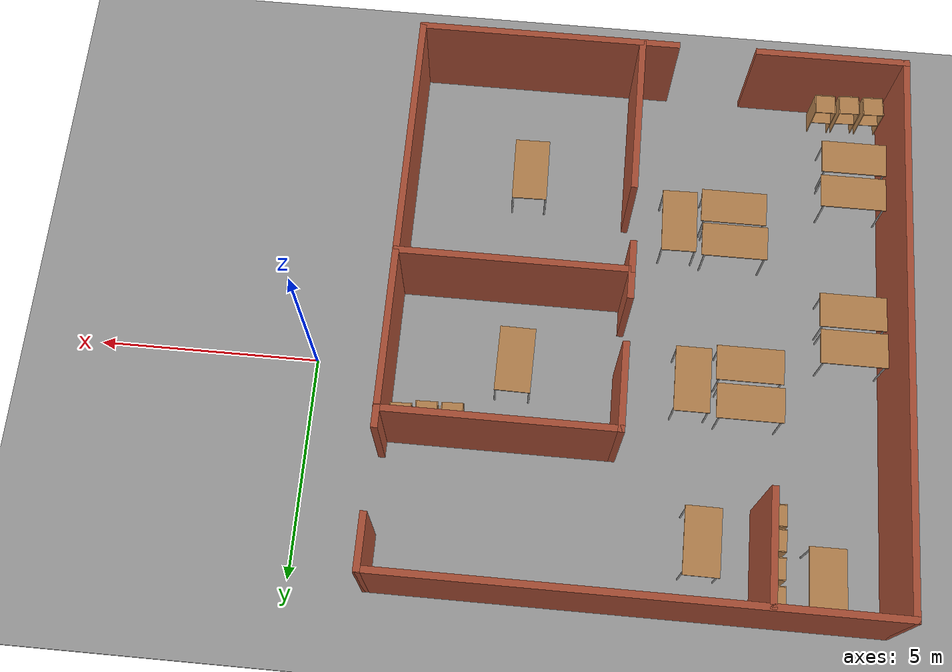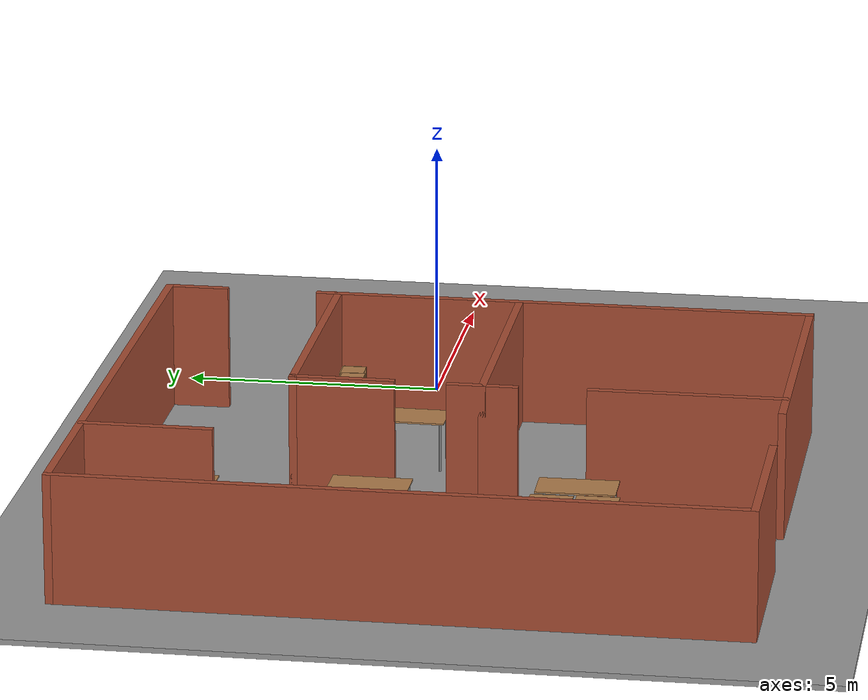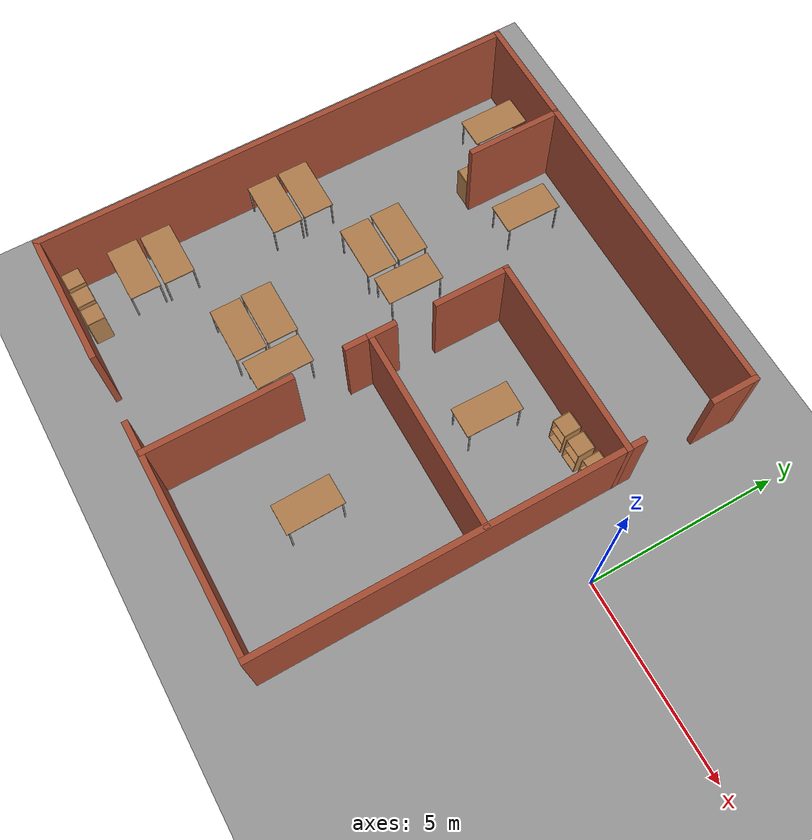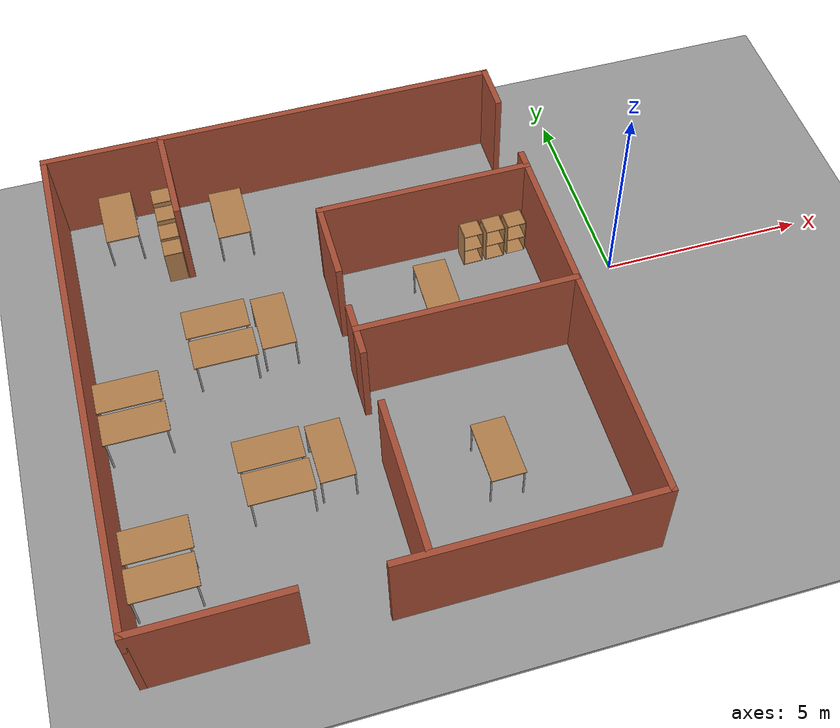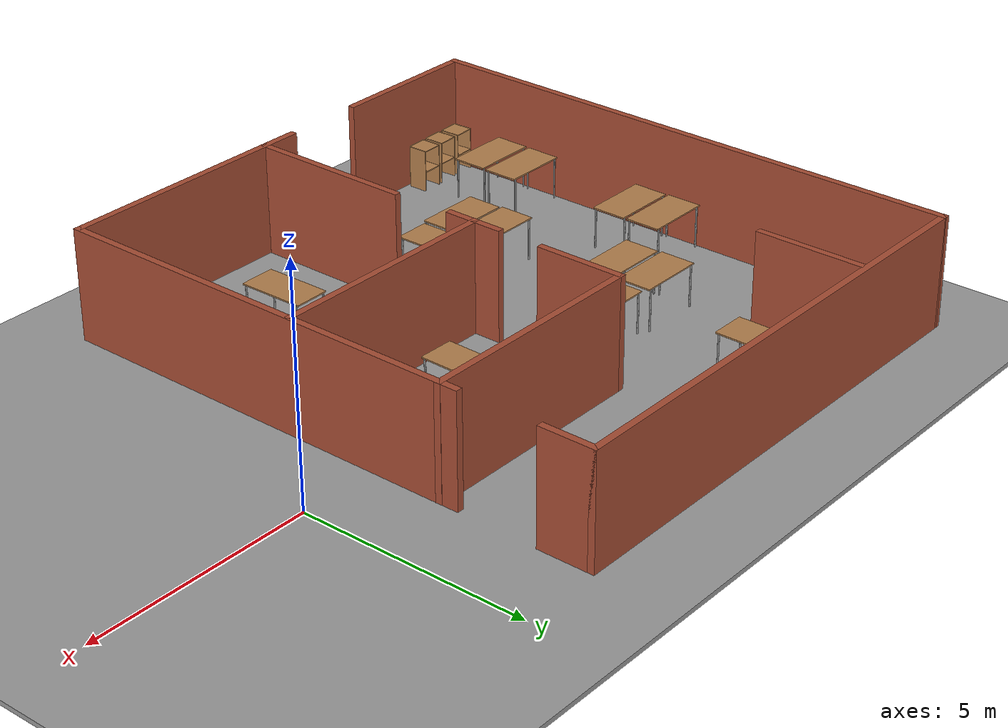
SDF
<sdf version="1.6">
 <world name="default">
  <light name="sun" type="directional">
   <pose>0 0 10 0 -0 0</pose>
   <diffuse>0.8 0.8 0.8 1</diffuse>
   <specular>0.2 0.2 0.2 1</specular>
   <attenuation>
    <range>1000</range>
    <constant>0.9</constant>
    <linear>0.01</linear>
    <quadratic>0.001</quadratic>
   </attenuation>
   <direction>-0.5 0.1 -0.9</direction>
  </light>
  <model name="ground_plane">
   <static>1</static>
   <link name="link">
    <collision name="collision">
     <geometry><plane><normal>0 0 1</normal><size>100 100</size></plane></geometry>
     <surface>
      <contact><collide_bitmask>65535</collide_bitmask></contact>
      <friction><ode><mu>100</mu><mu2>50</mu2></ode></friction>
     </surface>
    </collision>
    <visual name="visual">
     <cast_shadows>0</cast_shadows>
     <geometry><plane><normal>0 0 1</normal><size>100 100</size></plane></geometry>
     <material>
      <script><uri>file://media/materials/scripts/gazebo.material</uri><name>Gazebo/Grey</name></script>
     </material>
    </visual>
   </link>
  </model>
  <gravity>0 0 -9.8</gravity>
  <magnetic_field>6e-06 2.3e-05 -4.2e-05</magnetic_field>
  <atmosphere type="adiabatic"/>
  <physics name="default_physics" default="0" type="ode">
   <max_step_size>0.001</max_step_size>
   <real_time_factor>1</real_time_factor>
   <real_time_update_rate>1000</real_time_update_rate>
  </physics>
  <scene><ambient>0.4 0.4 0.4 1</ambient><background>0.7 0.7 0.7 1</background><shadows>1</shadows></scene>
  <audio><device>default</device></audio>
  <spherical_coordinates>
   <surface_model>EARTH_WGS84</surface_model>
   <latitude_deg>0</latitude_deg>
   <longitude_deg>0</longitude_deg>
   <elevation>0</elevation>
   <heading_deg>0</heading_deg>
  </spherical_coordinates>
  <model name="simple_office">
   <pose>-7.27757 -1.24508 0 0 -0 0</pose>
   <link name="Wall_18">
    <collision name="Wall_18_Collision">
     <geometry><box><size>12.75 0.15 2.5</size></box></geometry>
     <pose>0 0 1.25 0 -0 0</pose>
    </collision>
    <visual name="Wall_18_Visual">
     <pose>0 0 1.25 0 -0 0</pose>
     <geometry><box><size>12.75 0.15 2.5</size></box></geometry>
     <material>
      <script><uri>file://media/materials/scripts/gazebo.material</uri><name>Gazebo/Bricks</name></script>
      <ambient>1 1 1 1</ambient>
     </material>
     <meta><layer>0</layer></meta>
    </visual>
    <pose>-5.55213 0 0 0 -0 -1.5708</pose>
   </link>
   <link name="Wall_20">
    <collision name="Wall_20_Collision">
     <geometry><box><size>9.75 0.15 2.5</size></box></geometry>
     <pose>0 0 1.25 0 -0 0</pose>
    </collision>
    <visual name="Wall_20_Visual">
     <pose>0 0 1.25 0 -0 0</pose>
     <geometry><box><size>9.75 0.15 2.5</size></box></geometry>
     <material>
      <script><uri>file://media/materials/scripts/gazebo.material</uri><name>Gazebo/Bricks</name></script>
      <ambient>1 1 1 1</ambient>
     </material>
     <meta><layer>0</layer></meta>
    </visual>
    <pose>5.54787 -1.5 0 0 -0 1.5708</pose>
   </link>
   <link name="Wall_22">
    <collision name="Wall_22_Collision">
     <geometry><box><size>11.25 0.15 2.5</size></box></geometry>
     <pose>0 0 1.25 0 -0 0</pose>
    </collision>
    <visual name="Wall_22_Visual">
     <pose>0 0 1.25 0 -0 0</pose>
     <geometry><box><size>11.25 0.15 2.5</size></box></geometry>
     <material>
      <script><uri>file://media/materials/scripts/gazebo.material</uri><name>Gazebo/Bricks</name></script>
      <ambient>1 1 1 1</ambient>
     </material>
     <meta><layer>0</layer></meta>
    </visual>
    <pose>-0.002126 6.3 0 0 -0 0</pose>
   </link>
   <link name="Wall_23">
    <collision name="Wall_23_Collision">
     <geometry><box><size>1.25 0.15 2.5</size></box></geometry>
     <pose>0 0 1.25 0 -0 0</pose>
    </collision>
    <visual name="Wall_23_Visual">
     <pose>0 0 1.25 0 -0 0</pose>
     <geometry><box><size>1.25 0.15 2.5</size></box></geometry>
     <material>
      <script><uri>file://media/materials/scripts/gazebo.material</uri><name>Gazebo/Bricks</name></script>
      <ambient>1 1 1 1</ambient>
     </material>
     <meta><layer>0</layer></meta>
    </visual>
    <pose>5.54787 5.75 0 0 -0 -1.5708</pose>
   </link>
   <link name="Wall_25">
    <collision name="Wall_25_Collision">
     <geometry><box><size>5.25 0.15 2.5</size></box></geometry>
     <pose>0 0 1.25 0 -0 0</pose>
    </collision>
    <visual name="Wall_25_Visual">
     <pose>0 0 1.25 0 -0 0</pose>
     <geometry><box><size>5.25 0.15 2.5</size></box></geometry>
     <material>
      <script><uri>file://media/materials/scripts/gazebo.material</uri><name>Gazebo/Bricks</name></script>
      <ambient>1 1 1 1</ambient>
     </material>
     <meta><layer>0</layer></meta>
    </visual>
    <pose>3.00213 2.93507 0 0 -0 3.14159</pose>
   </link>
   <link name="Wall_26">
    <collision name="Wall_26_Collision">
     <geometry><box><size>2 0.15 2.5</size></box></geometry>
     <pose>0 0 1.25 0 -0 0</pose>
    </collision>
    <visual name="Wall_26_Visual">
     <pose>0 0 1.25 0 -0 0</pose>
     <geometry><box><size>2 0.15 2.5</size></box></geometry>
     <material>
      <script><uri>file://media/materials/scripts/gazebo.material</uri><name>Gazebo/Bricks</name></script>
      <ambient>1 1 1 1</ambient>
     </material>
     <meta><layer>0</layer></meta>
    </visual>
    <pose>0.452127 2.01008 0 0 -0 -1.5708</pose>
   </link>
   <link name="Wall_36">
    <collision name="Wall_36_Collision">
     <geometry><box><size>5.25 0.15 2.5</size></box></geometry>
     <pose>0 0 1.25 0 -0 0</pose>
    </collision>
    <visual name="Wall_36_Visual">
     <pose>0 0 1.25 0 -0 0</pose>
     <geometry><box><size>5.25 0.15 2.5</size></box></geometry>
     <material>
      <script><uri>file://media/materials/scripts/gazebo.material</uri><name>Gazebo/Bricks</name></script>
      <ambient>1 1 1 1</ambient>
     </material>
     <meta><layer>0</layer></meta>
    </visual>
    <pose>2.97154 -0.643982 0 0 -0 3.14159</pose>
   </link>
   <link name="Wall_37">
    <collision name="Wall_37_Collision">
     <geometry><box><size>0.75 0.15 2.5</size></box></geometry>
     <pose>0 0 1.25 0 -0 0</pose>
    </collision>
    <visual name="Wall_37_Visual">
     <pose>0 0 1.25 0 -0 0</pose>
     <geometry><box><size>0.75 0.15 2.5</size></box></geometry>
     <material>
      <script><uri>file://media/materials/scripts/gazebo.material</uri><name>Gazebo/Bricks</name></script>
      <ambient>1 1 1 1</ambient>
     </material>
     <meta><layer>0</layer></meta>
    </visual>
    <pose>0.421537 -0.343982 0 0 -0 1.5708</pose>
   </link>
   <link name="Wall_39">
    <collision name="Wall_39_Collision">
     <geometry><box><size>0.75 0.15 2.5</size></box></geometry>
     <pose>0 0 1.25 0 -0 0</pose>
    </collision>
    <visual name="Wall_39_Visual">
     <pose>0 0 1.25 0 -0 0</pose>
     <geometry><box><size>0.75 0.15 2.5</size></box></geometry>
     <material>
      <script><uri>file://media/materials/scripts/gazebo.material</uri><name>Gazebo/Bricks</name></script>
      <ambient>1 1 1 1</ambient>
     </material>
     <meta><layer>0</layer></meta>
    </visual>
    <pose>0.421537 -0.943982 0 0 -0 -1.5708</pose>
   </link>
   <link name="Wall_42">
    <collision name="Wall_42_Collision">
     <geometry><box><size>3.75 0.15 2.5</size></box></geometry>
     <pose>0 0 1.25 0 -0 0</pose>
    </collision>
    <visual name="Wall_42_Visual">
     <pose>0 0 1.25 0 -0 0</pose>
     <geometry><box><size>3.75 0.15 2.5</size></box></geometry>
     <material>
      <script><uri>file://media/materials/scripts/gazebo.material</uri><name>Gazebo/Bricks</name></script>
      <ambient>1 1 1 1</ambient>
     </material>
     <meta><layer>0</layer></meta>
    </visual>
    <pose>0.474149 -4.47258 0 0 -0 1.5708</pose>
   </link>
   <link name="Wall_44">
    <collision name="Wall_44_Collision">
     <geometry><box><size>3.5 0.15 2.5</size></box></geometry>
     <pose>0 0 1.25 0 -0 0</pose>
    </collision>
    <visual name="Wall_44_Visual">
     <pose>0 0 1.25 0 -0 0</pose>
     <geometry><box><size>3.5 0.15 2.5</size></box></geometry>
     <material>
      <script><uri>file://media/materials/scripts/gazebo.material</uri><name>Gazebo/Bricks</name></script>
      <ambient>1 1 1 1</ambient>
     </material>
     <meta><layer>0</layer></meta>
    </visual>
    <pose>-3.87713 -6.3 0 0 -0 0</pose>
   </link>
   <link name="Wall_46">
    <collision name="Wall_46_Collision">
     <geometry><box><size>6 0.15 2.5</size></box></geometry>
     <pose>0 0 1.25 0 -0 0</pose>
    </collision>
    <visual name="Wall_46_Visual">
     <pose>0 0 1.25 0 -0 0</pose>
     <geometry><box><size>6 0.15 2.5</size></box></geometry>
     <material>
      <script><uri>file://media/materials/scripts/gazebo.material</uri><name>Gazebo/Bricks</name></script>
      <ambient>1 1 1 1</ambient>
     </material>
     <meta><layer>0</layer></meta>
    </visual>
    <pose>2.62287 -6.3 0 0 -0 3.14159</pose>
   </link>
   <link name="Wall_48">
    <collision name="Wall_48_Collision">
     <geometry><box><size>2.5 0.15 2.5</size></box></geometry>
     <pose>0 0 1.25 0 -0 0</pose>
    </collision>
    <visual name="Wall_48_Visual">
     <pose>0 0 1.25 0 -0 0</pose>
     <geometry><box><size>2.5 0.15 2.5</size></box></geometry>
     <material>
      <script><uri>file://media/materials/scripts/gazebo.material</uri><name>Gazebo/Bricks</name></script>
      <ambient>1 1 1 1</ambient>
     </material>
     <meta><layer>0</layer></meta>
    </visual>
    <pose>-2.73782 5.09441 0 0 -0 -1.5708</pose>
   </link>
   <static>1</static>
  </model>
  <model name="ground_plane_0">
   <static>1</static>
   <link name="link">
    <collision name="collision">
     <geometry><plane><normal>0 0 1</normal><size>100 100</size></plane></geometry>
     <surface>
      <contact><collide_bitmask>65535</collide_bitmask></contact>
      <friction><ode><mu>100</mu><mu2>50</mu2></ode></friction>
     </surface>
    </collision>
    <visual name="visual">
     <cast_shadows>0</cast_shadows>
     <geometry><plane><normal>0 0 1</normal><size>100 100</size></plane></geometry>
     <material>
      <script><uri>file://media/materials/scripts/gazebo.material</uri><name>Gazebo/Grey</name></script>
     </material>
    </visual>
   </link>
   <pose>-11.7711 -0.848373 0 0 -0 0</pose>
  </model>
  <model name="table">
   <static>1</static>
   <link name="link">
    <collision name="surface">
     <pose>0 0 1 0 -0 0</pose>
     <geometry><box><size>1.5 0.8 0.03</size></box></geometry>
     <surface><friction><ode><mu>0.6</mu><mu2>0.6</mu2></ode></friction></surface>
    </collision>
    <visual name="visual1">
     <pose>0 0 1 0 -0 0</pose>
     <geometry><box><size>1.5 0.8 0.03</size></box></geometry>
     <material>
      <script><uri>file://media/materials/scripts/gazebo.material</uri><name>Gazebo/Wood</name></script>
     </material>
    </visual>
    <collision name="front_left_leg">
     <pose>0.68 0.38 0.5 0 -0 0</pose>
     <geometry><cylinder><radius>0.02</radius><length>1</length></cylinder></geometry>
    </collision>
    <visual name="front_left_leg">
     <pose>0.68 0.38 0.5 0 -0 0</pose>
     <geometry><cylinder><radius>0.02</radius><length>1</length></cylinder></geometry>
     <material>
      <script><uri>file://media/materials/scripts/gazebo.material</uri><name>Gazebo/Grey</name></script>
     </material>
    </visual>
    <collision name="front_right_leg">
     <pose>0.68 -0.38 0.5 0 -0 0</pose>
     <geometry><cylinder><radius>0.02</radius><length>1</length></cylinder></geometry>
    </collision>
    <visual name="front_right_leg">
     <pose>0.68 -0.38 0.5 0 -0 0</pose>
     <geometry><cylinder><radius>0.02</radius><length>1</length></cylinder></geometry>
     <material>
      <script><uri>file://media/materials/scripts/gazebo.material</uri><name>Gazebo/Grey</name></script>
     </material>
    </visual>
    <collision name="back_right_leg">
     <pose>-0.68 -0.38 0.5 0 -0 0</pose>
     <geometry><cylinder><radius>0.02</radius><length>1</length></cylinder></geometry>
    </collision>
    <visual name="back_right_leg">
     <pose>-0.68 -0.38 0.5 0 -0 0</pose>
     <geometry><cylinder><radius>0.02</radius><length>1</length></cylinder></geometry>
     <material>
      <script><uri>file://media/materials/scripts/gazebo.material</uri><name>Gazebo/Grey</name></script>
     </material>
    </visual>
    <collision name="back_left_leg">
     <pose>-0.68 0.38 0.5 0 -0 0</pose>
     <geometry><cylinder><radius>0.02</radius><length>1</length></cylinder></geometry>
    </collision>
    <visual name="back_left_leg">
     <pose>-0.68 0.38 0.5 0 -0 0</pose>
     <geometry><cylinder><radius>0.02</radius><length>1</length></cylinder></geometry>
     <material>
      <script><uri>file://media/materials/scripts/gazebo.material</uri><name>Gazebo/Grey</name></script>
     </material>
    </visual>
   </link>
   <pose>-11.4413 4.20939 0 0 0 -1.56565</pose>
  </model>
  <model name="cabinet">
   <static>1</static>
   <link name="cabinet_bottom_plate">
    <inertial>
     <pose>0 0 -1 0 -0 0</pose>
     <inertia><ixx>2.05</ixx><ixy>0</ixy><ixz>0</ixz><iyy>2.05</iyy><iyz>0</iyz><izz>2.05</izz></inertia>
     <mass>25</mass>
    </inertial>
    <collision name="cabinet_bottom_plate_geom">
     <pose>0 0 0.01 0 -0 0</pose>
     <geometry><box><size>0.45 0.45 0.02</size></box></geometry>
    </collision>
    <visual name="cabinet_bottom_plate_geom_visual">
     <pose>0 0 0.01 0 -0 0</pose>
     <geometry><box><size>0.45 0.45 0.02</size></box></geometry>
     <material>
      <script><uri>file://media/materials/scripts/gazebo.material</uri><name>Gazebo/Wood</name></script>
     </material>
    </visual>
    <collision name="cabinet_bottom_plate_geom_cabinet_back_plate">
     <pose>0.235 0 0.51 0 -0 0</pose>
     <geometry><box><size>0.02 0.45 1.02</size></box></geometry>
    </collision>
    <visual name="cabinet_bottom_plate_geom_cabinet_back_plate_visual">
     <pose>0.235 0 0.51 0 -0 0</pose>
     <geometry><box><size>0.02 0.45 1.02</size></box></geometry>
     <material>
      <script><uri>file://media/materials/scripts/gazebo.material</uri><name>Gazebo/Wood</name></script>
     </material>
    </visual>
    <collision name="cabinet_bottom_plate_geom_cabinet_left_plate">
     <pose>0 0.235 0.51 0 -0 0</pose>
     <geometry><box><size>0.45 0.02 1.02</size></box></geometry>
    </collision>
    <visual name="cabinet_bottom_plate_geom_cabinet_left_plate_visual">
     <pose>0 0.235 0.51 0 -0 0</pose>
     <geometry><box><size>0.45 0.02 1.02</size></box></geometry>
     <material>
      <script><uri>file://media/materials/scripts/gazebo.material</uri><name>Gazebo/Wood</name></script>
     </material>
    </visual>
    <collision name="cabinet_bottom_plate_geom_cabinet_middle_plate">
     <pose>0 0 0.51 0 -0 0</pose>
     <geometry><box><size>0.45 0.45 0.02</size></box></geometry>
    </collision>
    <visual name="cabinet_bottom_plate_geom_cabinet_middle_plate_visual">
     <pose>0 0 0.51 0 -0 0</pose>
     <geometry><box><size>0.45 0.45 0.02</size></box></geometry>
     <material>
      <script><uri>file://media/materials/scripts/gazebo.material</uri><name>Gazebo/Wood</name></script>
     </material>
    </visual>
    <collision name="cabinet_bottom_plate_geom_cabinet_right_plate">
     <pose>0 -0.235 0.51 0 -0 0</pose>
     <geometry><box><size>0.45 0.02 1.02</size></box></geometry>
    </collision>
    <visual name="cabinet_bottom_plate_geom_cabinet_right_plate_visual">
     <pose>0 -0.235 0.51 0 -0 0</pose>
     <geometry><box><size>0.45 0.02 1.02</size></box></geometry>
     <material>
      <script><uri>file://media/materials/scripts/gazebo.material</uri><name>Gazebo/Wood</name></script>
     </material>
    </visual>
    <collision name="cabinet_bottom_plate_geom_cabinet_top_plate">
     <pose>0 0 1.01 0 -0 0</pose>
     <geometry><box><size>0.45 0.45 0.02</size></box></geometry>
    </collision>
    <visual name="cabinet_bottom_plate_geom_cabinet_top_plate_visual">
     <pose>0 0 1.01 0 -0 0</pose>
     <geometry><box><size>0.45 0.45 0.02</size></box></geometry>
     <material>
      <script><uri>file://media/materials/scripts/gazebo.material</uri><name>Gazebo/Wood</name></script>
     </material>
    </visual>
   </link>
   <pose>-10.3428 2.85716 0 0 -0 0</pose>
  </model>
  <model name="cabinet_0">
   <static>1</static>
   <link name="cabinet_bottom_plate">
    <inertial>
     <pose>0 0 -1 0 -0 0</pose>
     <inertia><ixx>2.05</ixx><ixy>0</ixy><ixz>0</ixz><iyy>2.05</iyy><iyz>0</iyz><izz>2.05</izz></inertia>
     <mass>25</mass>
    </inertial>
    <collision name="cabinet_bottom_plate_geom">
     <pose>0 0 0.01 0 -0 0</pose>
     <geometry><box><size>0.45 0.45 0.02</size></box></geometry>
    </collision>
    <visual name="cabinet_bottom_plate_geom_visual">
     <pose>0 0 0.01 0 -0 0</pose>
     <geometry><box><size>0.45 0.45 0.02</size></box></geometry>
     <material>
      <script><uri>file://media/materials/scripts/gazebo.material</uri><name>Gazebo/Wood</name></script>
     </material>
    </visual>
    <collision name="cabinet_bottom_plate_geom_cabinet_back_plate">
     <pose>0.235 0 0.51 0 -0 0</pose>
     <geometry><box><size>0.02 0.45 1.02</size></box></geometry>
    </collision>
    <visual name="cabinet_bottom_plate_geom_cabinet_back_plate_visual">
     <pose>0.235 0 0.51 0 -0 0</pose>
     <geometry><box><size>0.02 0.45 1.02</size></box></geometry>
     <material>
      <script><uri>file://media/materials/scripts/gazebo.material</uri><name>Gazebo/Wood</name></script>
     </material>
    </visual>
    <collision name="cabinet_bottom_plate_geom_cabinet_left_plate">
     <pose>0 0.235 0.51 0 -0 0</pose>
     <geometry><box><size>0.45 0.02 1.02</size></box></geometry>
    </collision>
    <visual name="cabinet_bottom_plate_geom_cabinet_left_plate_visual">
     <pose>0 0.235 0.51 0 -0 0</pose>
     <geometry><box><size>0.45 0.02 1.02</size></box></geometry>
     <material>
      <script><uri>file://media/materials/scripts/gazebo.material</uri><name>Gazebo/Wood</name></script>
     </material>
    </visual>
    <collision name="cabinet_bottom_plate_geom_cabinet_middle_plate">
     <pose>0 0 0.51 0 -0 0</pose>
     <geometry><box><size>0.45 0.45 0.02</size></box></geometry>
    </collision>
    <visual name="cabinet_bottom_plate_geom_cabinet_middle_plate_visual">
     <pose>0 0 0.51 0 -0 0</pose>
     <geometry><box><size>0.45 0.45 0.02</size></box></geometry>
     <material>
      <script><uri>file://media/materials/scripts/gazebo.material</uri><name>Gazebo/Wood</name></script>
     </material>
    </visual>
    <collision name="cabinet_bottom_plate_geom_cabinet_right_plate">
     <pose>0 -0.235 0.51 0 -0 0</pose>
     <geometry><box><size>0.45 0.02 1.02</size></box></geometry>
    </collision>
    <visual name="cabinet_bottom_plate_geom_cabinet_right_plate_visual">
     <pose>0 -0.235 0.51 0 -0 0</pose>
     <geometry><box><size>0.45 0.02 1.02</size></box></geometry>
     <material>
      <script><uri>file://media/materials/scripts/gazebo.material</uri><name>Gazebo/Wood</name></script>
     </material>
    </visual>
    <collision name="cabinet_bottom_plate_geom_cabinet_top_plate">
     <pose>0 0 1.01 0 -0 0</pose>
     <geometry><box><size>0.45 0.45 0.02</size></box></geometry>
    </collision>
    <visual name="cabinet_bottom_plate_geom_cabinet_top_plate_visual">
     <pose>0 0 1.01 0 -0 0</pose>
     <geometry><box><size>0.45 0.45 0.02</size></box></geometry>
     <material>
      <script><uri>file://media/materials/scripts/gazebo.material</uri><name>Gazebo/Wood</name></script>
     </material>
    </visual>
   </link>
   <pose>-10.3414 3.39549 0 0 -0 0</pose>
  </model>
  <model name="cabinet_clone">
   <static>1</static>
   <link name="cabinet_bottom_plate">
    <inertial>
     <pose>0 0 -1 0 -0 0</pose>
     <inertia><ixx>2.05</ixx><ixy>0</ixy><ixz>0</ixz><iyy>2.05</iyy><iyz>0</iyz><izz>2.05</izz></inertia>
     <mass>25</mass>
    </inertial>
    <collision name="cabinet_bottom_plate_geom">
     <pose>0 0 0.01 0 -0 0</pose>
     <geometry><box><size>0.45 0.45 0.02</size></box></geometry>
    </collision>
    <visual name="cabinet_bottom_plate_geom_visual">
     <pose>0 0 0.01 0 -0 0</pose>
     <geometry><box><size>0.45 0.45 0.02</size></box></geometry>
     <material>
      <script><uri>file://media/materials/scripts/gazebo.material</uri><name>Gazebo/Wood</name></script>
     </material>
    </visual>
    <collision name="cabinet_bottom_plate_geom_cabinet_back_plate">
     <pose>0.235 0 0.51 0 -0 0</pose>
     <geometry><box><size>0.02 0.45 1.02</size></box></geometry>
    </collision>
    <visual name="cabinet_bottom_plate_geom_cabinet_back_plate_visual">
     <pose>0.235 0 0.51 0 -0 0</pose>
     <geometry><box><size>0.02 0.45 1.02</size></box></geometry>
     <material>
      <script><uri>file://media/materials/scripts/gazebo.material</uri><name>Gazebo/Wood</name></script>
     </material>
    </visual>
    <collision name="cabinet_bottom_plate_geom_cabinet_left_plate">
     <pose>0 0.235 0.51 0 -0 0</pose>
     <geometry><box><size>0.45 0.02 1.02</size></box></geometry>
    </collision>
    <visual name="cabinet_bottom_plate_geom_cabinet_left_plate_visual">
     <pose>0 0.235 0.51 0 -0 0</pose>
     <geometry><box><size>0.45 0.02 1.02</size></box></geometry>
     <material>
      <script><uri>file://media/materials/scripts/gazebo.material</uri><name>Gazebo/Wood</name></script>
     </material>
    </visual>
    <collision name="cabinet_bottom_plate_geom_cabinet_middle_plate">
     <pose>0 0 0.51 0 -0 0</pose>
     <geometry><box><size>0.45 0.45 0.02</size></box></geometry>
    </collision>
    <visual name="cabinet_bottom_plate_geom_cabinet_middle_plate_visual">
     <pose>0 0 0.51 0 -0 0</pose>
     <geometry><box><size>0.45 0.45 0.02</size></box></geometry>
     <material>
      <script><uri>file://media/materials/scripts/gazebo.material</uri><name>Gazebo/Wood</name></script>
     </material>
    </visual>
    <collision name="cabinet_bottom_plate_geom_cabinet_right_plate">
     <pose>0 -0.235 0.51 0 -0 0</pose>
     <geometry><box><size>0.45 0.02 1.02</size></box></geometry>
    </collision>
    <visual name="cabinet_bottom_plate_geom_cabinet_right_plate_visual">
     <pose>0 -0.235 0.51 0 -0 0</pose>
     <geometry><box><size>0.45 0.02 1.02</size></box></geometry>
     <material>
      <script><uri>file://media/materials/scripts/gazebo.material</uri><name>Gazebo/Wood</name></script>
     </material>
    </visual>
    <collision name="cabinet_bottom_plate_geom_cabinet_top_plate">
     <pose>0 0 1.01 0 -0 0</pose>
     <geometry><box><size>0.45 0.45 0.02</size></box></geometry>
    </collision>
    <visual name="cabinet_bottom_plate_geom_cabinet_top_plate_visual">
     <pose>0 0 1.01 0 -0 0</pose>
     <geometry><box><size>0.45 0.45 0.02</size></box></geometry>
     <material>
      <script><uri>file://media/materials/scripts/gazebo.material</uri><name>Gazebo/Wood</name></script>
     </material>
    </visual>
   </link>
   <pose>-10.3328 3.99527 0 0 -0 0</pose>
  </model>
  <model name="cabinet_clone_0">
   <static>1</static>
   <link name="cabinet_bottom_plate">
    <inertial>
     <pose>0 0 -1 0 -0 0</pose>
     <inertia><ixx>2.05</ixx><ixy>0</ixy><ixz>0</ixz><iyy>2.05</iyy><iyz>0</iyz><izz>2.05</izz></inertia>
     <mass>25</mass>
    </inertial>
    <collision name="cabinet_bottom_plate_geom">
     <pose>0 0 0.01 0 -0 0</pose>
     <geometry><box><size>0.45 0.45 0.02</size></box></geometry>
    </collision>
    <visual name="cabinet_bottom_plate_geom_visual">
     <pose>0 0 0.01 0 -0 0</pose>
     <geometry><box><size>0.45 0.45 0.02</size></box></geometry>
     <material>
      <script><uri>file://media/materials/scripts/gazebo.material</uri><name>Gazebo/Wood</name></script>
     </material>
    </visual>
    <collision name="cabinet_bottom_plate_geom_cabinet_back_plate">
     <pose>0.235 0 0.51 0 -0 0</pose>
     <geometry><box><size>0.02 0.45 1.02</size></box></geometry>
    </collision>
    <visual name="cabinet_bottom_plate_geom_cabinet_back_plate_visual">
     <pose>0.235 0 0.51 0 -0 0</pose>
     <geometry><box><size>0.02 0.45 1.02</size></box></geometry>
     <material>
      <script><uri>file://media/materials/scripts/gazebo.material</uri><name>Gazebo/Wood</name></script>
     </material>
    </visual>
    <collision name="cabinet_bottom_plate_geom_cabinet_left_plate">
     <pose>0 0.235 0.51 0 -0 0</pose>
     <geometry><box><size>0.45 0.02 1.02</size></box></geometry>
    </collision>
    <visual name="cabinet_bottom_plate_geom_cabinet_left_plate_visual">
     <pose>0 0.235 0.51 0 -0 0</pose>
     <geometry><box><size>0.45 0.02 1.02</size></box></geometry>
     <material>
      <script><uri>file://media/materials/scripts/gazebo.material</uri><name>Gazebo/Wood</name></script>
     </material>
    </visual>
    <collision name="cabinet_bottom_plate_geom_cabinet_middle_plate">
     <pose>0 0 0.51 0 -0 0</pose>
     <geometry><box><size>0.45 0.45 0.02</size></box></geometry>
    </collision>
    <visual name="cabinet_bottom_plate_geom_cabinet_middle_plate_visual">
     <pose>0 0 0.51 0 -0 0</pose>
     <geometry><box><size>0.45 0.45 0.02</size></box></geometry>
     <material>
      <script><uri>file://media/materials/scripts/gazebo.material</uri><name>Gazebo/Wood</name></script>
     </material>
    </visual>
    <collision name="cabinet_bottom_plate_geom_cabinet_right_plate">
     <pose>0 -0.235 0.51 0 -0 0</pose>
     <geometry><box><size>0.45 0.02 1.02</size></box></geometry>
    </collision>
    <visual name="cabinet_bottom_plate_geom_cabinet_right_plate_visual">
     <pose>0 -0.235 0.51 0 -0 0</pose>
     <geometry><box><size>0.45 0.02 1.02</size></box></geometry>
     <material>
      <script><uri>file://media/materials/scripts/gazebo.material</uri><name>Gazebo/Wood</name></script>
     </material>
    </visual>
    <collision name="cabinet_bottom_plate_geom_cabinet_top_plate">
     <pose>0 0 1.01 0 -0 0</pose>
     <geometry><box><size>0.45 0.45 0.02</size></box></geometry>
    </collision>
    <visual name="cabinet_bottom_plate_geom_cabinet_top_plate_visual">
     <pose>0 0 1.01 0 -0 0</pose>
     <geometry><box><size>0.45 0.45 0.02</size></box></geometry>
     <material>
      <script><uri>file://media/materials/scripts/gazebo.material</uri><name>Gazebo/Wood</name></script>
     </material>
    </visual>
   </link>
   <pose>-10.3382 4.60193 0 0 -0 0</pose>
  </model>
  <model name="table_0">
   <static>1</static>
   <link name="link">
    <collision name="surface">
     <pose>0 0 1 0 -0 0</pose>
     <geometry><box><size>1.5 0.8 0.03</size></box></geometry>
     <surface><friction><ode><mu>0.6</mu><mu2>0.6</mu2></ode></friction></surface>
    </collision>
    <visual name="visual1">
     <pose>0 0 1 0 -0 0</pose>
     <geometry><box><size>1.5 0.8 0.03</size></box></geometry>
     <material>
      <script><uri>file://media/materials/scripts/gazebo.material</uri><name>Gazebo/Wood</name></script>
     </material>
    </visual>
    <collision name="front_left_leg">
     <pose>0.68 0.38 0.5 0 -0 0</pose>
     <geometry><cylinder><radius>0.02</radius><length>1</length></cylinder></geometry>
    </collision>
    <visual name="front_left_leg">
     <pose>0.68 0.38 0.5 0 -0 0</pose>
     <geometry><cylinder><radius>0.02</radius><length>1</length></cylinder></geometry>
     <material>
      <script><uri>file://media/materials/scripts/gazebo.material</uri><name>Gazebo/Grey</name></script>
     </material>
    </visual>
    <collision name="front_right_leg">
     <pose>0.68 -0.38 0.5 0 -0 0</pose>
     <geometry><cylinder><radius>0.02</radius><length>1</length></cylinder></geometry>
    </collision>
    <visual name="front_right_leg">
     <pose>0.68 -0.38 0.5 0 -0 0</pose>
     <geometry><cylinder><radius>0.02</radius><length>1</length></cylinder></geometry>
     <material>
      <script><uri>file://media/materials/scripts/gazebo.material</uri><name>Gazebo/Grey</name></script>
     </material>
    </visual>
    <collision name="back_right_leg">
     <pose>-0.68 -0.38 0.5 0 -0 0</pose>
     <geometry><cylinder><radius>0.02</radius><length>1</length></cylinder></geometry>
    </collision>
    <visual name="back_right_leg">
     <pose>-0.68 -0.38 0.5 0 -0 0</pose>
     <geometry><cylinder><radius>0.02</radius><length>1</length></cylinder></geometry>
     <material>
      <script><uri>file://media/materials/scripts/gazebo.material</uri><name>Gazebo/Grey</name></script>
     </material>
    </visual>
    <collision name="back_left_leg">
     <pose>-0.68 0.38 0.5 0 -0 0</pose>
     <geometry><cylinder><radius>0.02</radius><length>1</length></cylinder></geometry>
    </collision>
    <visual name="back_left_leg">
     <pose>-0.68 0.38 0.5 0 -0 0</pose>
     <geometry><cylinder><radius>0.02</radius><length>1</length></cylinder></geometry>
     <material>
      <script><uri>file://media/materials/scripts/gazebo.material</uri><name>Gazebo/Grey</name></script>
     </material>
    </visual>
   </link>
   <pose>-8.78835 3.56308 0 0 -0 1.56265</pose>
  </model>
  <model name="table_1">
   <static>1</static>
   <link name="link">
    <collision name="surface">
     <pose>0 0 1 0 -0 0</pose>
     <geometry><box><size>1.5 0.8 0.03</size></box></geometry>
     <surface><friction><ode><mu>0.6</mu><mu2>0.6</mu2></ode></friction></surface>
    </collision>
    <visual name="visual1">
     <pose>0 0 1 0 -0 0</pose>
     <geometry><box><size>1.5 0.8 0.03</size></box></geometry>
     <material>
      <script><uri>file://media/materials/scripts/gazebo.material</uri><name>Gazebo/Wood</name></script>
     </material>
    </visual>
    <collision name="front_left_leg">
     <pose>0.68 0.38 0.5 0 -0 0</pose>
     <geometry><cylinder><radius>0.02</radius><length>1</length></cylinder></geometry>
    </collision>
    <visual name="front_left_leg">
     <pose>0.68 0.38 0.5 0 -0 0</pose>
     <geometry><cylinder><radius>0.02</radius><length>1</length></cylinder></geometry>
     <material>
      <script><uri>file://media/materials/scripts/gazebo.material</uri><name>Gazebo/Grey</name></script>
     </material>
    </visual>
    <collision name="front_right_leg">
     <pose>0.68 -0.38 0.5 0 -0 0</pose>
     <geometry><cylinder><radius>0.02</radius><length>1</length></cylinder></geometry>
    </collision>
    <visual name="front_right_leg">
     <pose>0.68 -0.38 0.5 0 -0 0</pose>
     <geometry><cylinder><radius>0.02</radius><length>1</length></cylinder></geometry>
     <material>
      <script><uri>file://media/materials/scripts/gazebo.material</uri><name>Gazebo/Grey</name></script>
     </material>
    </visual>
    <collision name="back_right_leg">
     <pose>-0.68 -0.38 0.5 0 -0 0</pose>
     <geometry><cylinder><radius>0.02</radius><length>1</length></cylinder></geometry>
    </collision>
    <visual name="back_right_leg">
     <pose>-0.68 -0.38 0.5 0 -0 0</pose>
     <geometry><cylinder><radius>0.02</radius><length>1</length></cylinder></geometry>
     <material>
      <script><uri>file://media/materials/scripts/gazebo.material</uri><name>Gazebo/Grey</name></script>
     </material>
    </visual>
    <collision name="back_left_leg">
     <pose>-0.68 0.38 0.5 0 -0 0</pose>
     <geometry><cylinder><radius>0.02</radius><length>1</length></cylinder></geometry>
    </collision>
    <visual name="back_left_leg">
     <pose>-0.68 0.38 0.5 0 -0 0</pose>
     <geometry><cylinder><radius>0.02</radius><length>1</length></cylinder></geometry>
     <material>
      <script><uri>file://media/materials/scripts/gazebo.material</uri><name>Gazebo/Grey</name></script>
     </material>
    </visual>
   </link>
   <pose>-4.50688 -0.122222 0 0 -0 1.55727</pose>
  </model>
  <model name="table_2">
   <static>1</static>
   <link name="link">
    <collision name="surface">
     <pose>0 0 1 0 -0 0</pose>
     <geometry><box><size>1.5 0.8 0.03</size></box></geometry>
     <surface><friction><ode><mu>0.6</mu><mu2>0.6</mu2></ode></friction></surface>
    </collision>
    <visual name="visual1">
     <pose>0 0 1 0 -0 0</pose>
     <geometry><box><size>1.5 0.8 0.03</size></box></geometry>
     <material>
      <script><uri>file://media/materials/scripts/gazebo.material</uri><name>Gazebo/Wood</name></script>
     </material>
    </visual>
    <collision name="front_left_leg">
     <pose>0.68 0.38 0.5 0 -0 0</pose>
     <geometry><cylinder><radius>0.02</radius><length>1</length></cylinder></geometry>
    </collision>
    <visual name="front_left_leg">
     <pose>0.68 0.38 0.5 0 -0 0</pose>
     <geometry><cylinder><radius>0.02</radius><length>1</length></cylinder></geometry>
     <material>
      <script><uri>file://media/materials/scripts/gazebo.material</uri><name>Gazebo/Grey</name></script>
     </material>
    </visual>
    <collision name="front_right_leg">
     <pose>0.68 -0.38 0.5 0 -0 0</pose>
     <geometry><cylinder><radius>0.02</radius><length>1</length></cylinder></geometry>
    </collision>
    <visual name="front_right_leg">
     <pose>0.68 -0.38 0.5 0 -0 0</pose>
     <geometry><cylinder><radius>0.02</radius><length>1</length></cylinder></geometry>
     <material>
      <script><uri>file://media/materials/scripts/gazebo.material</uri><name>Gazebo/Grey</name></script>
     </material>
    </visual>
    <collision name="back_right_leg">
     <pose>-0.68 -0.38 0.5 0 -0 0</pose>
     <geometry><cylinder><radius>0.02</radius><length>1</length></cylinder></geometry>
    </collision>
    <visual name="back_right_leg">
     <pose>-0.68 -0.38 0.5 0 -0 0</pose>
     <geometry><cylinder><radius>0.02</radius><length>1</length></cylinder></geometry>
     <material>
      <script><uri>file://media/materials/scripts/gazebo.material</uri><name>Gazebo/Grey</name></script>
     </material>
    </visual>
    <collision name="back_left_leg">
     <pose>-0.68 0.38 0.5 0 -0 0</pose>
     <geometry><cylinder><radius>0.02</radius><length>1</length></cylinder></geometry>
    </collision>
    <visual name="back_left_leg">
     <pose>-0.68 0.38 0.5 0 -0 0</pose>
     <geometry><cylinder><radius>0.02</radius><length>1</length></cylinder></geometry>
     <material>
      <script><uri>file://media/materials/scripts/gazebo.material</uri><name>Gazebo/Grey</name></script>
     </material>
    </visual>
   </link>
   <pose>-4.4903 -4.8204 0 0 -0 1.58773</pose>
  </model>
  <model name="table_3">
   <static>1</static>
   <link name="link">
    <collision name="surface">
     <pose>0 0 1 0 -0 0</pose>
     <geometry><box><size>1.5 0.8 0.03</size></box></geometry>
     <surface><friction><ode><mu>0.6</mu><mu2>0.6</mu2></ode></friction></surface>
    </collision>
    <visual name="visual1">
     <pose>0 0 1 0 -0 0</pose>
     <geometry><box><size>1.5 0.8 0.03</size></box></geometry>
     <material>
      <script><uri>file://media/materials/scripts/gazebo.material</uri><name>Gazebo/Wood</name></script>
     </material>
    </visual>
    <collision name="front_left_leg">
     <pose>0.68 0.38 0.5 0 -0 0</pose>
     <geometry><cylinder><radius>0.02</radius><length>1</length></cylinder></geometry>
    </collision>
    <visual name="front_left_leg">
     <pose>0.68 0.38 0.5 0 -0 0</pose>
     <geometry><cylinder><radius>0.02</radius><length>1</length></cylinder></geometry>
     <material>
      <script><uri>file://media/materials/scripts/gazebo.material</uri><name>Gazebo/Grey</name></script>
     </material>
    </visual>
    <collision name="front_right_leg">
     <pose>0.68 -0.38 0.5 0 -0 0</pose>
     <geometry><cylinder><radius>0.02</radius><length>1</length></cylinder></geometry>
    </collision>
    <visual name="front_right_leg">
     <pose>0.68 -0.38 0.5 0 -0 0</pose>
     <geometry><cylinder><radius>0.02</radius><length>1</length></cylinder></geometry>
     <material>
      <script><uri>file://media/materials/scripts/gazebo.material</uri><name>Gazebo/Grey</name></script>
     </material>
    </visual>
    <collision name="back_right_leg">
     <pose>-0.68 -0.38 0.5 0 -0 0</pose>
     <geometry><cylinder><radius>0.02</radius><length>1</length></cylinder></geometry>
    </collision>
    <visual name="back_right_leg">
     <pose>-0.68 -0.38 0.5 0 -0 0</pose>
     <geometry><cylinder><radius>0.02</radius><length>1</length></cylinder></geometry>
     <material>
      <script><uri>file://media/materials/scripts/gazebo.material</uri><name>Gazebo/Grey</name></script>
     </material>
    </visual>
    <collision name="back_left_leg">
     <pose>-0.68 0.38 0.5 0 -0 0</pose>
     <geometry><cylinder><radius>0.02</radius><length>1</length></cylinder></geometry>
    </collision>
    <visual name="back_left_leg">
     <pose>-0.68 0.38 0.5 0 -0 0</pose>
     <geometry><cylinder><radius>0.02</radius><length>1</length></cylinder></geometry>
     <material>
      <script><uri>file://media/materials/scripts/gazebo.material</uri><name>Gazebo/Grey</name></script>
     </material>
    </visual>
   </link>
   <pose>-9.73659 0.414798 0 0 -0 0</pose>
  </model>
  <model name="table_4">
   <static>1</static>
   <link name="link">
    <collision name="surface">
     <pose>0 0 1 0 -0 0</pose>
     <geometry><box><size>1.5 0.8 0.03</size></box></geometry>
     <surface><friction><ode><mu>0.6</mu><mu2>0.6</mu2></ode></friction></surface>
    </collision>
    <visual name="visual1">
     <pose>0 0 1 0 -0 0</pose>
     <geometry><box><size>1.5 0.8 0.03</size></box></geometry>
     <material>
      <script><uri>file://media/materials/scripts/gazebo.material</uri><name>Gazebo/Wood</name></script>
     </material>
    </visual>
    <collision name="front_left_leg">
     <pose>0.68 0.38 0.5 0 -0 0</pose>
     <geometry><cylinder><radius>0.02</radius><length>1</length></cylinder></geometry>
    </collision>
    <visual name="front_left_leg">
     <pose>0.68 0.38 0.5 0 -0 0</pose>
     <geometry><cylinder><radius>0.02</radius><length>1</length></cylinder></geometry>
     <material>
      <script><uri>file://media/materials/scripts/gazebo.material</uri><name>Gazebo/Grey</name></script>
     </material>
    </visual>
    <collision name="front_right_leg">
     <pose>0.68 -0.38 0.5 0 -0 0</pose>
     <geometry><cylinder><radius>0.02</radius><length>1</length></cylinder></geometry>
    </collision>
    <visual name="front_right_leg">
     <pose>0.68 -0.38 0.5 0 -0 0</pose>
     <geometry><cylinder><radius>0.02</radius><length>1</length></cylinder></geometry>
     <material>
      <script><uri>file://media/materials/scripts/gazebo.material</uri><name>Gazebo/Grey</name></script>
     </material>
    </visual>
    <collision name="back_right_leg">
     <pose>-0.68 -0.38 0.5 0 -0 0</pose>
     <geometry><cylinder><radius>0.02</radius><length>1</length></cylinder></geometry>
    </collision>
    <visual name="back_right_leg">
     <pose>-0.68 -0.38 0.5 0 -0 0</pose>
     <geometry><cylinder><radius>0.02</radius><length>1</length></cylinder></geometry>
     <material>
      <script><uri>file://media/materials/scripts/gazebo.material</uri><name>Gazebo/Grey</name></script>
     </material>
    </visual>
    <collision name="back_left_leg">
     <pose>-0.68 0.38 0.5 0 -0 0</pose>
     <geometry><cylinder><radius>0.02</radius><length>1</length></cylinder></geometry>
    </collision>
    <visual name="back_left_leg">
     <pose>-0.68 0.38 0.5 0 -0 0</pose>
     <geometry><cylinder><radius>0.02</radius><length>1</length></cylinder></geometry>
     <material>
      <script><uri>file://media/materials/scripts/gazebo.material</uri><name>Gazebo/Grey</name></script>
     </material>
    </visual>
   </link>
   <pose>-9.70839 -0.466215 0 0 -0 0</pose>
  </model>
  <model name="table_5">
   <static>1</static>
   <link name="link">
    <collision name="surface">
     <pose>0 0 1 0 -0 0</pose>
     <geometry><box><size>1.5 0.8 0.03</size></box></geometry>
     <surface><friction><ode><mu>0.6</mu><mu2>0.6</mu2></ode></friction></surface>
    </collision>
    <visual name="visual1">
     <pose>0 0 1 0 -0 0</pose>
     <geometry><box><size>1.5 0.8 0.03</size></box></geometry>
     <material>
      <script><uri>file://media/materials/scripts/gazebo.material</uri><name>Gazebo/Wood</name></script>
     </material>
    </visual>
    <collision name="front_left_leg">
     <pose>0.68 0.38 0.5 0 -0 0</pose>
     <geometry><cylinder><radius>0.02</radius><length>1</length></cylinder></geometry>
    </collision>
    <visual name="front_left_leg">
     <pose>0.68 0.38 0.5 0 -0 0</pose>
     <geometry><cylinder><radius>0.02</radius><length>1</length></cylinder></geometry>
     <material>
      <script><uri>file://media/materials/scripts/gazebo.material</uri><name>Gazebo/Grey</name></script>
     </material>
    </visual>
    <collision name="front_right_leg">
     <pose>0.68 -0.38 0.5 0 -0 0</pose>
     <geometry><cylinder><radius>0.02</radius><length>1</length></cylinder></geometry>
    </collision>
    <visual name="front_right_leg">
     <pose>0.68 -0.38 0.5 0 -0 0</pose>
     <geometry><cylinder><radius>0.02</radius><length>1</length></cylinder></geometry>
     <material>
      <script><uri>file://media/materials/scripts/gazebo.material</uri><name>Gazebo/Grey</name></script>
     </material>
    </visual>
    <collision name="back_right_leg">
     <pose>-0.68 -0.38 0.5 0 -0 0</pose>
     <geometry><cylinder><radius>0.02</radius><length>1</length></cylinder></geometry>
    </collision>
    <visual name="back_right_leg">
     <pose>-0.68 -0.38 0.5 0 -0 0</pose>
     <geometry><cylinder><radius>0.02</radius><length>1</length></cylinder></geometry>
     <material>
      <script><uri>file://media/materials/scripts/gazebo.material</uri><name>Gazebo/Grey</name></script>
     </material>
    </visual>
    <collision name="back_left_leg">
     <pose>-0.68 0.38 0.5 0 -0 0</pose>
     <geometry><cylinder><radius>0.02</radius><length>1</length></cylinder></geometry>
    </collision>
    <visual name="back_left_leg">
     <pose>-0.68 0.38 0.5 0 -0 0</pose>
     <geometry><cylinder><radius>0.02</radius><length>1</length></cylinder></geometry>
     <material>
      <script><uri>file://media/materials/scripts/gazebo.material</uri><name>Gazebo/Grey</name></script>
     </material>
    </visual>
   </link>
   <pose>-8.45015 -0.01693 0 0 0 -1.57161</pose>
  </model>
  <model name="table_6">
   <static>1</static>
   <link name="link">
    <collision name="surface">
     <pose>0 0 1 0 -0 0</pose>
     <geometry><box><size>1.5 0.8 0.03</size></box></geometry>
     <surface><friction><ode><mu>0.6</mu><mu2>0.6</mu2></ode></friction></surface>
    </collision>
    <visual name="visual1">
     <pose>0 0 1 0 -0 0</pose>
     <geometry><box><size>1.5 0.8 0.03</size></box></geometry>
     <material>
      <script><uri>file://media/materials/scripts/gazebo.material</uri><name>Gazebo/Wood</name></script>
     </material>
    </visual>
    <collision name="front_left_leg">
     <pose>0.68 0.38 0.5 0 -0 0</pose>
     <geometry><cylinder><radius>0.02</radius><length>1</length></cylinder></geometry>
    </collision>
    <visual name="front_left_leg">
     <pose>0.68 0.38 0.5 0 -0 0</pose>
     <geometry><cylinder><radius>0.02</radius><length>1</length></cylinder></geometry>
     <material>
      <script><uri>file://media/materials/scripts/gazebo.material</uri><name>Gazebo/Grey</name></script>
     </material>
    </visual>
    <collision name="front_right_leg">
     <pose>0.68 -0.38 0.5 0 -0 0</pose>
     <geometry><cylinder><radius>0.02</radius><length>1</length></cylinder></geometry>
    </collision>
    <visual name="front_right_leg">
     <pose>0.68 -0.38 0.5 0 -0 0</pose>
     <geometry><cylinder><radius>0.02</radius><length>1</length></cylinder></geometry>
     <material>
      <script><uri>file://media/materials/scripts/gazebo.material</uri><name>Gazebo/Grey</name></script>
     </material>
    </visual>
    <collision name="back_right_leg">
     <pose>-0.68 -0.38 0.5 0 -0 0</pose>
     <geometry><cylinder><radius>0.02</radius><length>1</length></cylinder></geometry>
    </collision>
    <visual name="back_right_leg">
     <pose>-0.68 -0.38 0.5 0 -0 0</pose>
     <geometry><cylinder><radius>0.02</radius><length>1</length></cylinder></geometry>
     <material>
      <script><uri>file://media/materials/scripts/gazebo.material</uri><name>Gazebo/Grey</name></script>
     </material>
    </visual>
    <collision name="back_left_leg">
     <pose>-0.68 0.38 0.5 0 -0 0</pose>
     <geometry><cylinder><radius>0.02</radius><length>1</length></cylinder></geometry>
    </collision>
    <visual name="back_left_leg">
     <pose>-0.68 0.38 0.5 0 -0 0</pose>
     <geometry><cylinder><radius>0.02</radius><length>1</length></cylinder></geometry>
     <material>
      <script><uri>file://media/materials/scripts/gazebo.material</uri><name>Gazebo/Grey</name></script>
     </material>
    </visual>
   </link>
   <pose>-9.28377 -3.42263 0 0 -0 0</pose>
  </model>
  <model name="table_7">
   <static>1</static>
   <link name="link">
    <collision name="surface">
     <pose>0 0 1 0 -0 0</pose>
     <geometry><box><size>1.5 0.8 0.03</size></box></geometry>
     <surface><friction><ode><mu>0.6</mu><mu2>0.6</mu2></ode></friction></surface>
    </collision>
    <visual name="visual1">
     <pose>0 0 1 0 -0 0</pose>
     <geometry><box><size>1.5 0.8 0.03</size></box></geometry>
     <material>
      <script><uri>file://media/materials/scripts/gazebo.material</uri><name>Gazebo/Wood</name></script>
     </material>
    </visual>
    <collision name="front_left_leg">
     <pose>0.68 0.38 0.5 0 -0 0</pose>
     <geometry><cylinder><radius>0.02</radius><length>1</length></cylinder></geometry>
    </collision>
    <visual name="front_left_leg">
     <pose>0.68 0.38 0.5 0 -0 0</pose>
     <geometry><cylinder><radius>0.02</radius><length>1</length></cylinder></geometry>
     <material>
      <script><uri>file://media/materials/scripts/gazebo.material</uri><name>Gazebo/Grey</name></script>
     </material>
    </visual>
    <collision name="front_right_leg">
     <pose>0.68 -0.38 0.5 0 -0 0</pose>
     <geometry><cylinder><radius>0.02</radius><length>1</length></cylinder></geometry>
    </collision>
    <visual name="front_right_leg">
     <pose>0.68 -0.38 0.5 0 -0 0</pose>
     <geometry><cylinder><radius>0.02</radius><length>1</length></cylinder></geometry>
     <material>
      <script><uri>file://media/materials/scripts/gazebo.material</uri><name>Gazebo/Grey</name></script>
     </material>
    </visual>
    <collision name="back_right_leg">
     <pose>-0.68 -0.38 0.5 0 -0 0</pose>
     <geometry><cylinder><radius>0.02</radius><length>1</length></cylinder></geometry>
    </collision>
    <visual name="back_right_leg">
     <pose>-0.68 -0.38 0.5 0 -0 0</pose>
     <geometry><cylinder><radius>0.02</radius><length>1</length></cylinder></geometry>
     <material>
      <script><uri>file://media/materials/scripts/gazebo.material</uri><name>Gazebo/Grey</name></script>
     </material>
    </visual>
    <collision name="back_left_leg">
     <pose>-0.68 0.38 0.5 0 -0 0</pose>
     <geometry><cylinder><radius>0.02</radius><length>1</length></cylinder></geometry>
    </collision>
    <visual name="back_left_leg">
     <pose>-0.68 0.38 0.5 0 -0 0</pose>
     <geometry><cylinder><radius>0.02</radius><length>1</length></cylinder></geometry>
     <material>
      <script><uri>file://media/materials/scripts/gazebo.material</uri><name>Gazebo/Grey</name></script>
     </material>
    </visual>
   </link>
   <pose>-9.23972 -4.27415 0 0 -0 0</pose>
  </model>
  <model name="table_8">
   <static>1</static>
   <link name="link">
    <collision name="surface">
     <pose>0 0 1 0 -0 0</pose>
     <geometry><box><size>1.5 0.8 0.03</size></box></geometry>
     <surface><friction><ode><mu>0.6</mu><mu2>0.6</mu2></ode></friction></surface>
    </collision>
    <visual name="visual1">
     <pose>0 0 1 0 -0 0</pose>
     <geometry><box><size>1.5 0.8 0.03</size></box></geometry>
     <material>
      <script><uri>file://media/materials/scripts/gazebo.material</uri><name>Gazebo/Wood</name></script>
     </material>
    </visual>
    <collision name="front_left_leg">
     <pose>0.68 0.38 0.5 0 -0 0</pose>
     <geometry><cylinder><radius>0.02</radius><length>1</length></cylinder></geometry>
    </collision>
    <visual name="front_left_leg">
     <pose>0.68 0.38 0.5 0 -0 0</pose>
     <geometry><cylinder><radius>0.02</radius><length>1</length></cylinder></geometry>
     <material>
      <script><uri>file://media/materials/scripts/gazebo.material</uri><name>Gazebo/Grey</name></script>
     </material>
    </visual>
    <collision name="front_right_leg">
     <pose>0.68 -0.38 0.5 0 -0 0</pose>
     <geometry><cylinder><radius>0.02</radius><length>1</length></cylinder></geometry>
    </collision>
    <visual name="front_right_leg">
     <pose>0.68 -0.38 0.5 0 -0 0</pose>
     <geometry><cylinder><radius>0.02</radius><length>1</length></cylinder></geometry>
     <material>
      <script><uri>file://media/materials/scripts/gazebo.material</uri><name>Gazebo/Grey</name></script>
     </material>
    </visual>
    <collision name="back_right_leg">
     <pose>-0.68 -0.38 0.5 0 -0 0</pose>
     <geometry><cylinder><radius>0.02</radius><length>1</length></cylinder></geometry>
    </collision>
    <visual name="back_right_leg">
     <pose>-0.68 -0.38 0.5 0 -0 0</pose>
     <geometry><cylinder><radius>0.02</radius><length>1</length></cylinder></geometry>
     <material>
      <script><uri>file://media/materials/scripts/gazebo.material</uri><name>Gazebo/Grey</name></script>
     </material>
    </visual>
    <collision name="back_left_leg">
     <pose>-0.68 0.38 0.5 0 -0 0</pose>
     <geometry><cylinder><radius>0.02</radius><length>1</length></cylinder></geometry>
    </collision>
    <visual name="back_left_leg">
     <pose>-0.68 0.38 0.5 0 -0 0</pose>
     <geometry><cylinder><radius>0.02</radius><length>1</length></cylinder></geometry>
     <material>
      <script><uri>file://media/materials/scripts/gazebo.material</uri><name>Gazebo/Grey</name></script>
     </material>
    </visual>
   </link>
   <pose>-8.00187 -3.82124 0 0 0 -1.55463</pose>
  </model>
  <model name="table_9">
   <static>1</static>
   <link name="link">
    <collision name="surface">
     <pose>0 0 1 0 -0 0</pose>
     <geometry><box><size>1.5 0.8 0.03</size></box></geometry>
     <surface><friction><ode><mu>0.6</mu><mu2>0.6</mu2></ode></friction></surface>
    </collision>
    <visual name="visual1">
     <pose>0 0 1 0 -0 0</pose>
     <geometry><box><size>1.5 0.8 0.03</size></box></geometry>
     <material>
      <script><uri>file://media/materials/scripts/gazebo.material</uri><name>Gazebo/Wood</name></script>
     </material>
    </visual>
    <collision name="front_left_leg">
     <pose>0.68 0.38 0.5 0 -0 0</pose>
     <geometry><cylinder><radius>0.02</radius><length>1</length></cylinder></geometry>
    </collision>
    <visual name="front_left_leg">
     <pose>0.68 0.38 0.5 0 -0 0</pose>
     <geometry><cylinder><radius>0.02</radius><length>1</length></cylinder></geometry>
     <material>
      <script><uri>file://media/materials/scripts/gazebo.material</uri><name>Gazebo/Grey</name></script>
     </material>
    </visual>
    <collision name="front_right_leg">
     <pose>0.68 -0.38 0.5 0 -0 0</pose>
     <geometry><cylinder><radius>0.02</radius><length>1</length></cylinder></geometry>
    </collision>
    <visual name="front_right_leg">
     <pose>0.68 -0.38 0.5 0 -0 0</pose>
     <geometry><cylinder><radius>0.02</radius><length>1</length></cylinder></geometry>
     <material>
      <script><uri>file://media/materials/scripts/gazebo.material</uri><name>Gazebo/Grey</name></script>
     </material>
    </visual>
    <collision name="back_right_leg">
     <pose>-0.68 -0.38 0.5 0 -0 0</pose>
     <geometry><cylinder><radius>0.02</radius><length>1</length></cylinder></geometry>
    </collision>
    <visual name="back_right_leg">
     <pose>-0.68 -0.38 0.5 0 -0 0</pose>
     <geometry><cylinder><radius>0.02</radius><length>1</length></cylinder></geometry>
     <material>
      <script><uri>file://media/materials/scripts/gazebo.material</uri><name>Gazebo/Grey</name></script>
     </material>
    </visual>
    <collision name="back_left_leg">
     <pose>-0.68 0.38 0.5 0 -0 0</pose>
     <geometry><cylinder><radius>0.02</radius><length>1</length></cylinder></geometry>
    </collision>
    <visual name="back_left_leg">
     <pose>-0.68 0.38 0.5 0 -0 0</pose>
     <geometry><cylinder><radius>0.02</radius><length>1</length></cylinder></geometry>
     <material>
      <script><uri>file://media/materials/scripts/gazebo.material</uri><name>Gazebo/Grey</name></script>
     </material>
    </visual>
   </link>
   <pose>-12.0078 -5.79647 0 0 -0 0</pose>
  </model>
  <model name="table_10">
   <static>1</static>
   <link name="link">
    <collision name="surface">
     <pose>0 0 1 0 -0 0</pose>
     <geometry><box><size>1.5 0.8 0.03</size></box></geometry>
     <surface><friction><ode><mu>0.6</mu><mu2>0.6</mu2></ode></friction></surface>
    </collision>
    <visual name="visual1">
     <pose>0 0 1 0 -0 0</pose>
     <geometry><box><size>1.5 0.8 0.03</size></box></geometry>
     <material>
      <script><uri>file://media/materials/scripts/gazebo.material</uri><name>Gazebo/Wood</name></script>
     </material>
    </visual>
    <collision name="front_left_leg">
     <pose>0.68 0.38 0.5 0 -0 0</pose>
     <geometry><cylinder><radius>0.02</radius><length>1</length></cylinder></geometry>
    </collision>
    <visual name="front_left_leg">
     <pose>0.68 0.38 0.5 0 -0 0</pose>
     <geometry><cylinder><radius>0.02</radius><length>1</length></cylinder></geometry>
     <material>
      <script><uri>file://media/materials/scripts/gazebo.material</uri><name>Gazebo/Grey</name></script>
     </material>
    </visual>
    <collision name="front_right_leg">
     <pose>0.68 -0.38 0.5 0 -0 0</pose>
     <geometry><cylinder><radius>0.02</radius><length>1</length></cylinder></geometry>
    </collision>
    <visual name="front_right_leg">
     <pose>0.68 -0.38 0.5 0 -0 0</pose>
     <geometry><cylinder><radius>0.02</radius><length>1</length></cylinder></geometry>
     <material>
      <script><uri>file://media/materials/scripts/gazebo.material</uri><name>Gazebo/Grey</name></script>
     </material>
    </visual>
    <collision name="back_right_leg">
     <pose>-0.68 -0.38 0.5 0 -0 0</pose>
     <geometry><cylinder><radius>0.02</radius><length>1</length></cylinder></geometry>
    </collision>
    <visual name="back_right_leg">
     <pose>-0.68 -0.38 0.5 0 -0 0</pose>
     <geometry><cylinder><radius>0.02</radius><length>1</length></cylinder></geometry>
     <material>
      <script><uri>file://media/materials/scripts/gazebo.material</uri><name>Gazebo/Grey</name></script>
     </material>
    </visual>
    <collision name="back_left_leg">
     <pose>-0.68 0.38 0.5 0 -0 0</pose>
     <geometry><cylinder><radius>0.02</radius><length>1</length></cylinder></geometry>
    </collision>
    <visual name="back_left_leg">
     <pose>-0.68 0.38 0.5 0 -0 0</pose>
     <geometry><cylinder><radius>0.02</radius><length>1</length></cylinder></geometry>
     <material>
      <script><uri>file://media/materials/scripts/gazebo.material</uri><name>Gazebo/Grey</name></script>
     </material>
    </visual>
   </link>
   <pose>-11.9913 -4.90278 0 0 -0 0</pose>
  </model>
  <model name="table_11">
   <static>1</static>
   <link name="link">
    <collision name="surface">
     <pose>0 0 1 0 -0 0</pose>
     <geometry><box><size>1.5 0.8 0.03</size></box></geometry>
     <surface><friction><ode><mu>0.6</mu><mu2>0.6</mu2></ode></friction></surface>
    </collision>
    <visual name="visual1">
     <pose>0 0 1 0 -0 0</pose>
     <geometry><box><size>1.5 0.8 0.03</size></box></geometry>
     <material>
      <script><uri>file://media/materials/scripts/gazebo.material</uri><name>Gazebo/Wood</name></script>
     </material>
    </visual>
    <collision name="front_left_leg">
     <pose>0.68 0.38 0.5 0 -0 0</pose>
     <geometry><cylinder><radius>0.02</radius><length>1</length></cylinder></geometry>
    </collision>
    <visual name="front_left_leg">
     <pose>0.68 0.38 0.5 0 -0 0</pose>
     <geometry><cylinder><radius>0.02</radius><length>1</length></cylinder></geometry>
     <material>
      <script><uri>file://media/materials/scripts/gazebo.material</uri><name>Gazebo/Grey</name></script>
     </material>
    </visual>
    <collision name="front_right_leg">
     <pose>0.68 -0.38 0.5 0 -0 0</pose>
     <geometry><cylinder><radius>0.02</radius><length>1</length></cylinder></geometry>
    </collision>
    <visual name="front_right_leg">
     <pose>0.68 -0.38 0.5 0 -0 0</pose>
     <geometry><cylinder><radius>0.02</radius><length>1</length></cylinder></geometry>
     <material>
      <script><uri>file://media/materials/scripts/gazebo.material</uri><name>Gazebo/Grey</name></script>
     </material>
    </visual>
    <collision name="back_right_leg">
     <pose>-0.68 -0.38 0.5 0 -0 0</pose>
     <geometry><cylinder><radius>0.02</radius><length>1</length></cylinder></geometry>
    </collision>
    <visual name="back_right_leg">
     <pose>-0.68 -0.38 0.5 0 -0 0</pose>
     <geometry><cylinder><radius>0.02</radius><length>1</length></cylinder></geometry>
     <material>
      <script><uri>file://media/materials/scripts/gazebo.material</uri><name>Gazebo/Grey</name></script>
     </material>
    </visual>
    <collision name="back_left_leg">
     <pose>-0.68 0.38 0.5 0 -0 0</pose>
     <geometry><cylinder><radius>0.02</radius><length>1</length></cylinder></geometry>
    </collision>
    <visual name="back_left_leg">
     <pose>-0.68 0.38 0.5 0 -0 0</pose>
     <geometry><cylinder><radius>0.02</radius><length>1</length></cylinder></geometry>
     <material>
      <script><uri>file://media/materials/scripts/gazebo.material</uri><name>Gazebo/Grey</name></script>
     </material>
    </visual>
   </link>
   <pose>-11.9824 -1.92544 0 0 -0 0</pose>
  </model>
  <model name="table_12">
   <static>1</static>
   <link name="link">
    <collision name="surface">
     <pose>0 0 1 0 -0 0</pose>
     <geometry><box><size>1.5 0.8 0.03</size></box></geometry>
     <surface><friction><ode><mu>0.6</mu><mu2>0.6</mu2></ode></friction></surface>
    </collision>
    <visual name="visual1">
     <pose>0 0 1 0 -0 0</pose>
     <geometry><box><size>1.5 0.8 0.03</size></box></geometry>
     <material>
      <script><uri>file://media/materials/scripts/gazebo.material</uri><name>Gazebo/Wood</name></script>
     </material>
    </visual>
    <collision name="front_left_leg">
     <pose>0.68 0.38 0.5 0 -0 0</pose>
     <geometry><cylinder><radius>0.02</radius><length>1</length></cylinder></geometry>
    </collision>
    <visual name="front_left_leg">
     <pose>0.68 0.38 0.5 0 -0 0</pose>
     <geometry><cylinder><radius>0.02</radius><length>1</length></cylinder></geometry>
     <material>
      <script><uri>file://media/materials/scripts/gazebo.material</uri><name>Gazebo/Grey</name></script>
     </material>
    </visual>
    <collision name="front_right_leg">
     <pose>0.68 -0.38 0.5 0 -0 0</pose>
     <geometry><cylinder><radius>0.02</radius><length>1</length></cylinder></geometry>
    </collision>
    <visual name="front_right_leg">
     <pose>0.68 -0.38 0.5 0 -0 0</pose>
     <geometry><cylinder><radius>0.02</radius><length>1</length></cylinder></geometry>
     <material>
      <script><uri>file://media/materials/scripts/gazebo.material</uri><name>Gazebo/Grey</name></script>
     </material>
    </visual>
    <collision name="back_right_leg">
     <pose>-0.68 -0.38 0.5 0 -0 0</pose>
     <geometry><cylinder><radius>0.02</radius><length>1</length></cylinder></geometry>
    </collision>
    <visual name="back_right_leg">
     <pose>-0.68 -0.38 0.5 0 -0 0</pose>
     <geometry><cylinder><radius>0.02</radius><length>1</length></cylinder></geometry>
     <material>
      <script><uri>file://media/materials/scripts/gazebo.material</uri><name>Gazebo/Grey</name></script>
     </material>
    </visual>
    <collision name="back_left_leg">
     <pose>-0.68 0.38 0.5 0 -0 0</pose>
     <geometry><cylinder><radius>0.02</radius><length>1</length></cylinder></geometry>
    </collision>
    <visual name="back_left_leg">
     <pose>-0.68 0.38 0.5 0 -0 0</pose>
     <geometry><cylinder><radius>0.02</radius><length>1</length></cylinder></geometry>
     <material>
      <script><uri>file://media/materials/scripts/gazebo.material</uri><name>Gazebo/Grey</name></script>
     </material>
    </visual>
   </link>
   <pose>-12.0025 -1.05655 0 0 -0 0</pose>
  </model>
  <model name="cabinet_1">
   <static>1</static>
   <link name="cabinet_bottom_plate">
    <inertial>
     <pose>0 0 -1 0 -0 0</pose>
     <inertia><ixx>2.05</ixx><ixy>0</ixy><ixz>0</ixz><iyy>2.05</iyy><iyz>0</iyz><izz>2.05</izz></inertia>
     <mass>25</mass>
    </inertial>
    <collision name="cabinet_bottom_plate_geom">
     <pose>0 0 0.01 0 -0 0</pose>
     <geometry><box><size>0.45 0.45 0.02</size></box></geometry>
    </collision>
    <visual name="cabinet_bottom_plate_geom_visual">
     <pose>0 0 0.01 0 -0 0</pose>
     <geometry><box><size>0.45 0.45 0.02</size></box></geometry>
     <material>
      <script><uri>file://media/materials/scripts/gazebo.material</uri><name>Gazebo/Wood</name></script>
     </material>
    </visual>
    <collision name="cabinet_bottom_plate_geom_cabinet_back_plate">
     <pose>0.235 0 0.51 0 -0 0</pose>
     <geometry><box><size>0.02 0.45 1.02</size></box></geometry>
    </collision>
    <visual name="cabinet_bottom_plate_geom_cabinet_back_plate_visual">
     <pose>0.235 0 0.51 0 -0 0</pose>
     <geometry><box><size>0.02 0.45 1.02</size></box></geometry>
     <material>
      <script><uri>file://media/materials/scripts/gazebo.material</uri><name>Gazebo/Wood</name></script>
     </material>
    </visual>
    <collision name="cabinet_bottom_plate_geom_cabinet_left_plate">
     <pose>0 0.235 0.51 0 -0 0</pose>
     <geometry><box><size>0.45 0.02 1.02</size></box></geometry>
    </collision>
    <visual name="cabinet_bottom_plate_geom_cabinet_left_plate_visual">
     <pose>0 0.235 0.51 0 -0 0</pose>
     <geometry><box><size>0.45 0.02 1.02</size></box></geometry>
     <material>
      <script><uri>file://media/materials/scripts/gazebo.material</uri><name>Gazebo/Wood</name></script>
     </material>
    </visual>
    <collision name="cabinet_bottom_plate_geom_cabinet_middle_plate">
     <pose>0 0 0.51 0 -0 0</pose>
     <geometry><box><size>0.45 0.45 0.02</size></box></geometry>
    </collision>
    <visual name="cabinet_bottom_plate_geom_cabinet_middle_plate_visual">
     <pose>0 0 0.51 0 -0 0</pose>
     <geometry><box><size>0.45 0.45 0.02</size></box></geometry>
     <material>
      <script><uri>file://media/materials/scripts/gazebo.material</uri><name>Gazebo/Wood</name></script>
     </material>
    </visual>
    <collision name="cabinet_bottom_plate_geom_cabinet_right_plate">
     <pose>0 -0.235 0.51 0 -0 0</pose>
     <geometry><box><size>0.45 0.02 1.02</size></box></geometry>
    </collision>
    <visual name="cabinet_bottom_plate_geom_cabinet_right_plate_visual">
     <pose>0 -0.235 0.51 0 -0 0</pose>
     <geometry><box><size>0.45 0.02 1.02</size></box></geometry>
     <material>
      <script><uri>file://media/materials/scripts/gazebo.material</uri><name>Gazebo/Wood</name></script>
     </material>
    </visual>
    <collision name="cabinet_bottom_plate_geom_cabinet_top_plate">
     <pose>0 0 1.01 0 -0 0</pose>
     <geometry><box><size>0.45 0.45 0.02</size></box></geometry>
    </collision>
    <visual name="cabinet_bottom_plate_geom_cabinet_top_plate_visual">
     <pose>0 0 1.01 0 -0 0</pose>
     <geometry><box><size>0.45 0.45 0.02</size></box></geometry>
     <material>
      <script><uri>file://media/materials/scripts/gazebo.material</uri><name>Gazebo/Wood</name></script>
     </material>
    </visual>
   </link>
   <pose>-12.4622 -7.20653 0 0 0 -1.5257</pose>
  </model>
  <model name="cabinet_2">
   <static>1</static>
   <link name="cabinet_bottom_plate">
    <inertial>
     <pose>0 0 -1 0 -0 0</pose>
     <inertia><ixx>2.05</ixx><ixy>0</ixy><ixz>0</ixz><iyy>2.05</iyy><iyz>0</iyz><izz>2.05</izz></inertia>
     <mass>25</mass>
    </inertial>
    <collision name="cabinet_bottom_plate_geom">
     <pose>0 0 0.01 0 -0 0</pose>
     <geometry><box><size>0.45 0.45 0.02</size></box></geometry>
    </collision>
    <visual name="cabinet_bottom_plate_geom_visual">
     <pose>0 0 0.01 0 -0 0</pose>
     <geometry><box><size>0.45 0.45 0.02</size></box></geometry>
     <material>
      <script><uri>file://media/materials/scripts/gazebo.material</uri><name>Gazebo/Wood</name></script>
     </material>
    </visual>
    <collision name="cabinet_bottom_plate_geom_cabinet_back_plate">
     <pose>0.235 0 0.51 0 -0 0</pose>
     <geometry><box><size>0.02 0.45 1.02</size></box></geometry>
    </collision>
    <visual name="cabinet_bottom_plate_geom_cabinet_back_plate_visual">
     <pose>0.235 0 0.51 0 -0 0</pose>
     <geometry><box><size>0.02 0.45 1.02</size></box></geometry>
     <material>
      <script><uri>file://media/materials/scripts/gazebo.material</uri><name>Gazebo/Wood</name></script>
     </material>
    </visual>
    <collision name="cabinet_bottom_plate_geom_cabinet_left_plate">
     <pose>0 0.235 0.51 0 -0 0</pose>
     <geometry><box><size>0.45 0.02 1.02</size></box></geometry>
    </collision>
    <visual name="cabinet_bottom_plate_geom_cabinet_left_plate_visual">
     <pose>0 0.235 0.51 0 -0 0</pose>
     <geometry><box><size>0.45 0.02 1.02</size></box></geometry>
     <material>
      <script><uri>file://media/materials/scripts/gazebo.material</uri><name>Gazebo/Wood</name></script>
     </material>
    </visual>
    <collision name="cabinet_bottom_plate_geom_cabinet_middle_plate">
     <pose>0 0 0.51 0 -0 0</pose>
     <geometry><box><size>0.45 0.45 0.02</size></box></geometry>
    </collision>
    <visual name="cabinet_bottom_plate_geom_cabinet_middle_plate_visual">
     <pose>0 0 0.51 0 -0 0</pose>
     <geometry><box><size>0.45 0.45 0.02</size></box></geometry>
     <material>
      <script><uri>file://media/materials/scripts/gazebo.material</uri><name>Gazebo/Wood</name></script>
     </material>
    </visual>
    <collision name="cabinet_bottom_plate_geom_cabinet_right_plate">
     <pose>0 -0.235 0.51 0 -0 0</pose>
     <geometry><box><size>0.45 0.02 1.02</size></box></geometry>
    </collision>
    <visual name="cabinet_bottom_plate_geom_cabinet_right_plate_visual">
     <pose>0 -0.235 0.51 0 -0 0</pose>
     <geometry><box><size>0.45 0.02 1.02</size></box></geometry>
     <material>
      <script><uri>file://media/materials/scripts/gazebo.material</uri><name>Gazebo/Wood</name></script>
     </material>
    </visual>
    <collision name="cabinet_bottom_plate_geom_cabinet_top_plate">
     <pose>0 0 1.01 0 -0 0</pose>
     <geometry><box><size>0.45 0.45 0.02</size></box></geometry>
    </collision>
    <visual name="cabinet_bottom_plate_geom_cabinet_top_plate_visual">
     <pose>0 0 1.01 0 -0 0</pose>
     <geometry><box><size>0.45 0.45 0.02</size></box></geometry>
     <material>
      <script><uri>file://media/materials/scripts/gazebo.material</uri><name>Gazebo/Wood</name></script>
     </material>
    </visual>
   </link>
   <pose>-11.8939 -7.1946 0 0 0 -1.52927</pose>
  </model>
  <model name="cabinet_3">
   <static>1</static>
   <link name="cabinet_bottom_plate">
    <inertial>
     <pose>0 0 -1 0 -0 0</pose>
     <inertia><ixx>2.05</ixx><ixy>0</ixy><ixz>0</ixz><iyy>2.05</iyy><iyz>0</iyz><izz>2.05</izz></inertia>
     <mass>25</mass>
    </inertial>
    <collision name="cabinet_bottom_plate_geom">
     <pose>0 0 0.01 0 -0 0</pose>
     <geometry><box><size>0.45 0.45 0.02</size></box></geometry>
    </collision>
    <visual name="cabinet_bottom_plate_geom_visual">
     <pose>0 0 0.01 0 -0 0</pose>
     <geometry><box><size>0.45 0.45 0.02</size></box></geometry>
     <material>
      <script><uri>file://media/materials/scripts/gazebo.material</uri><name>Gazebo/Wood</name></script>
     </material>
    </visual>
    <collision name="cabinet_bottom_plate_geom_cabinet_back_plate">
     <pose>0.235 0 0.51 0 -0 0</pose>
     <geometry><box><size>0.02 0.45 1.02</size></box></geometry>
    </collision>
    <visual name="cabinet_bottom_plate_geom_cabinet_back_plate_visual">
     <pose>0.235 0 0.51 0 -0 0</pose>
     <geometry><box><size>0.02 0.45 1.02</size></box></geometry>
     <material>
      <script><uri>file://media/materials/scripts/gazebo.material</uri><name>Gazebo/Wood</name></script>
     </material>
    </visual>
    <collision name="cabinet_bottom_plate_geom_cabinet_left_plate">
     <pose>0 0.235 0.51 0 -0 0</pose>
     <geometry><box><size>0.45 0.02 1.02</size></box></geometry>
    </collision>
    <visual name="cabinet_bottom_plate_geom_cabinet_left_plate_visual">
     <pose>0 0.235 0.51 0 -0 0</pose>
     <geometry><box><size>0.45 0.02 1.02</size></box></geometry>
     <material>
      <script><uri>file://media/materials/scripts/gazebo.material</uri><name>Gazebo/Wood</name></script>
     </material>
    </visual>
    <collision name="cabinet_bottom_plate_geom_cabinet_middle_plate">
     <pose>0 0 0.51 0 -0 0</pose>
     <geometry><box><size>0.45 0.45 0.02</size></box></geometry>
    </collision>
    <visual name="cabinet_bottom_plate_geom_cabinet_middle_plate_visual">
     <pose>0 0 0.51 0 -0 0</pose>
     <geometry><box><size>0.45 0.45 0.02</size></box></geometry>
     <material>
      <script><uri>file://media/materials/scripts/gazebo.material</uri><name>Gazebo/Wood</name></script>
     </material>
    </visual>
    <collision name="cabinet_bottom_plate_geom_cabinet_right_plate">
     <pose>0 -0.235 0.51 0 -0 0</pose>
     <geometry><box><size>0.45 0.02 1.02</size></box></geometry>
    </collision>
    <visual name="cabinet_bottom_plate_geom_cabinet_right_plate_visual">
     <pose>0 -0.235 0.51 0 -0 0</pose>
     <geometry><box><size>0.45 0.02 1.02</size></box></geometry>
     <material>
      <script><uri>file://media/materials/scripts/gazebo.material</uri><name>Gazebo/Wood</name></script>
     </material>
    </visual>
    <collision name="cabinet_bottom_plate_geom_cabinet_top_plate">
     <pose>0 0 1.01 0 -0 0</pose>
     <geometry><box><size>0.45 0.45 0.02</size></box></geometry>
    </collision>
    <visual name="cabinet_bottom_plate_geom_cabinet_top_plate_visual">
     <pose>0 0 1.01 0 -0 0</pose>
     <geometry><box><size>0.45 0.45 0.02</size></box></geometry>
     <material>
      <script><uri>file://media/materials/scripts/gazebo.material</uri><name>Gazebo/Wood</name></script>
     </material>
    </visual>
   </link>
   <pose>-11.3344 -7.17057 0 0 0 -1.55264</pose>
  </model>
  <model name="cabinet_4">
   <static>1</static>
   <link name="cabinet_bottom_plate">
    <inertial>
     <pose>0 0 -1 0 -0 0</pose>
     <inertia><ixx>2.05</ixx><ixy>0</ixy><ixz>0</ixz><iyy>2.05</iyy><iyz>0</iyz><izz>2.05</izz></inertia>
     <mass>25</mass>
    </inertial>
    <collision name="cabinet_bottom_plate_geom">
     <pose>0 0 0.01 0 -0 0</pose>
     <geometry><box><size>0.45 0.45 0.02</size></box></geometry>
    </collision>
    <visual name="cabinet_bottom_plate_geom_visual">
     <pose>0 0 0.01 0 -0 0</pose>
     <geometry><box><size>0.45 0.45 0.02</size></box></geometry>
     <material>
      <script><uri>file://media/materials/scripts/gazebo.material</uri><name>Gazebo/Wood</name></script>
     </material>
    </visual>
    <collision name="cabinet_bottom_plate_geom_cabinet_back_plate">
     <pose>0.235 0 0.51 0 -0 0</pose>
     <geometry><box><size>0.02 0.45 1.02</size></box></geometry>
    </collision>
    <visual name="cabinet_bottom_plate_geom_cabinet_back_plate_visual">
     <pose>0.235 0 0.51 0 -0 0</pose>
     <geometry><box><size>0.02 0.45 1.02</size></box></geometry>
     <material>
      <script><uri>file://media/materials/scripts/gazebo.material</uri><name>Gazebo/Wood</name></script>
     </material>
    </visual>
    <collision name="cabinet_bottom_plate_geom_cabinet_left_plate">
     <pose>0 0.235 0.51 0 -0 0</pose>
     <geometry><box><size>0.45 0.02 1.02</size></box></geometry>
    </collision>
    <visual name="cabinet_bottom_plate_geom_cabinet_left_plate_visual">
     <pose>0 0.235 0.51 0 -0 0</pose>
     <geometry><box><size>0.45 0.02 1.02</size></box></geometry>
     <material>
      <script><uri>file://media/materials/scripts/gazebo.material</uri><name>Gazebo/Wood</name></script>
     </material>
    </visual>
    <collision name="cabinet_bottom_plate_geom_cabinet_middle_plate">
     <pose>0 0 0.51 0 -0 0</pose>
     <geometry><box><size>0.45 0.45 0.02</size></box></geometry>
    </collision>
    <visual name="cabinet_bottom_plate_geom_cabinet_middle_plate_visual">
     <pose>0 0 0.51 0 -0 0</pose>
     <geometry><box><size>0.45 0.45 0.02</size></box></geometry>
     <material>
      <script><uri>file://media/materials/scripts/gazebo.material</uri><name>Gazebo/Wood</name></script>
     </material>
    </visual>
    <collision name="cabinet_bottom_plate_geom_cabinet_right_plate">
     <pose>0 -0.235 0.51 0 -0 0</pose>
     <geometry><box><size>0.45 0.02 1.02</size></box></geometry>
    </collision>
    <visual name="cabinet_bottom_plate_geom_cabinet_right_plate_visual">
     <pose>0 -0.235 0.51 0 -0 0</pose>
     <geometry><box><size>0.45 0.02 1.02</size></box></geometry>
     <material>
      <script><uri>file://media/materials/scripts/gazebo.material</uri><name>Gazebo/Wood</name></script>
     </material>
    </visual>
    <collision name="cabinet_bottom_plate_geom_cabinet_top_plate">
     <pose>0 0 1.01 0 -0 0</pose>
     <geometry><box><size>0.45 0.45 0.02</size></box></geometry>
    </collision>
    <visual name="cabinet_bottom_plate_geom_cabinet_top_plate_visual">
     <pose>0 0 1.01 0 -0 0</pose>
     <geometry><box><size>0.45 0.45 0.02</size></box></geometry>
     <material>
      <script><uri>file://media/materials/scripts/gazebo.material</uri><name>Gazebo/Wood</name></script>
     </material>
    </visual>
   </link>
   <pose>-2.10496 1.34334 0.031572 0 -0 1.59732</pose>
  </model>
  <model name="cabinet_4_clone">
   <static>1</static>
   <link name="cabinet_bottom_plate">
    <inertial>
     <pose>0 0 -1 0 -0 0</pose>
     <inertia><ixx>2.05</ixx><ixy>0</ixy><ixz>0</ixz><iyy>2.05</iyy><iyz>0</iyz><izz>2.05</izz></inertia>
     <mass>25</mass>
    </inertial>
    <collision name="cabinet_bottom_plate_geom">
     <pose>0 0 0.01 0 -0 0</pose>
     <geometry><box><size>0.45 0.45 0.02</size></box></geometry>
    </collision>
    <visual name="cabinet_bottom_plate_geom_visual">
     <pose>0 0 0.01 0 -0 0</pose>
     <geometry><box><size>0.45 0.45 0.02</size></box></geometry>
     <material>
      <script><uri>file://media/materials/scripts/gazebo.material</uri><name>Gazebo/Wood</name></script>
     </material>
    </visual>
    <collision name="cabinet_bottom_plate_geom_cabinet_back_plate">
     <pose>0.235 0 0.51 0 -0 0</pose>
     <geometry><box><size>0.02 0.45 1.02</size></box></geometry>
    </collision>
    <visual name="cabinet_bottom_plate_geom_cabinet_back_plate_visual">
     <pose>0.235 0 0.51 0 -0 0</pose>
     <geometry><box><size>0.02 0.45 1.02</size></box></geometry>
     <material>
      <script><uri>file://media/materials/scripts/gazebo.material</uri><name>Gazebo/Wood</name></script>
     </material>
    </visual>
    <collision name="cabinet_bottom_plate_geom_cabinet_left_plate">
     <pose>0 0.235 0.51 0 -0 0</pose>
     <geometry><box><size>0.45 0.02 1.02</size></box></geometry>
    </collision>
    <visual name="cabinet_bottom_plate_geom_cabinet_left_plate_visual">
     <pose>0 0.235 0.51 0 -0 0</pose>
     <geometry><box><size>0.45 0.02 1.02</size></box></geometry>
     <material>
      <script><uri>file://media/materials/scripts/gazebo.material</uri><name>Gazebo/Wood</name></script>
     </material>
    </visual>
    <collision name="cabinet_bottom_plate_geom_cabinet_middle_plate">
     <pose>0 0 0.51 0 -0 0</pose>
     <geometry><box><size>0.45 0.45 0.02</size></box></geometry>
    </collision>
    <visual name="cabinet_bottom_plate_geom_cabinet_middle_plate_visual">
     <pose>0 0 0.51 0 -0 0</pose>
     <geometry><box><size>0.45 0.45 0.02</size></box></geometry>
     <material>
      <script><uri>file://media/materials/scripts/gazebo.material</uri><name>Gazebo/Wood</name></script>
     </material>
    </visual>
    <collision name="cabinet_bottom_plate_geom_cabinet_right_plate">
     <pose>0 -0.235 0.51 0 -0 0</pose>
     <geometry><box><size>0.45 0.02 1.02</size></box></geometry>
    </collision>
    <visual name="cabinet_bottom_plate_geom_cabinet_right_plate_visual">
     <pose>0 -0.235 0.51 0 -0 0</pose>
     <geometry><box><size>0.45 0.02 1.02</size></box></geometry>
     <material>
      <script><uri>file://media/materials/scripts/gazebo.material</uri><name>Gazebo/Wood</name></script>
     </material>
    </visual>
    <collision name="cabinet_bottom_plate_geom_cabinet_top_plate">
     <pose>0 0 1.01 0 -0 0</pose>
     <geometry><box><size>0.45 0.45 0.02</size></box></geometry>
    </collision>
    <visual name="cabinet_bottom_plate_geom_cabinet_top_plate_visual">
     <pose>0 0 1.01 0 -0 0</pose>
     <geometry><box><size>0.45 0.45 0.02</size></box></geometry>
     <material>
      <script><uri>file://media/materials/scripts/gazebo.material</uri><name>Gazebo/Wood</name></script>
     </material>
    </visual>
   </link>
   <pose>-2.67442 1.27413 0.088689 0 -0 1.59732</pose>
  </model>
  <model name="cabinet_4_clone_0">
   <static>1</static>
   <link name="cabinet_bottom_plate">
    <inertial>
     <pose>0 0 -1 0 -0 0</pose>
     <inertia><ixx>2.05</ixx><ixy>0</ixy><ixz>0</ixz><iyy>2.05</iyy><iyz>0</iyz><izz>2.05</izz></inertia>
     <mass>25</mass>
    </inertial>
    <collision name="cabinet_bottom_plate_geom">
     <pose>0 0 0.01 0 -0 0</pose>
     <geometry><box><size>0.45 0.45 0.02</size></box></geometry>
    </collision>
    <visual name="cabinet_bottom_plate_geom_visual">
     <pose>0 0 0.01 0 -0 0</pose>
     <geometry><box><size>0.45 0.45 0.02</size></box></geometry>
     <material>
      <script><uri>file://media/materials/scripts/gazebo.material</uri><name>Gazebo/Wood</name></script>
     </material>
    </visual>
    <collision name="cabinet_bottom_plate_geom_cabinet_back_plate">
     <pose>0.235 0 0.51 0 -0 0</pose>
     <geometry><box><size>0.02 0.45 1.02</size></box></geometry>
    </collision>
    <visual name="cabinet_bottom_plate_geom_cabinet_back_plate_visual">
     <pose>0.235 0 0.51 0 -0 0</pose>
     <geometry><box><size>0.02 0.45 1.02</size></box></geometry>
     <material>
      <script><uri>file://media/materials/scripts/gazebo.material</uri><name>Gazebo/Wood</name></script>
     </material>
    </visual>
    <collision name="cabinet_bottom_plate_geom_cabinet_left_plate">
     <pose>0 0.235 0.51 0 -0 0</pose>
     <geometry><box><size>0.45 0.02 1.02</size></box></geometry>
    </collision>
    <visual name="cabinet_bottom_plate_geom_cabinet_left_plate_visual">
     <pose>0 0.235 0.51 0 -0 0</pose>
     <geometry><box><size>0.45 0.02 1.02</size></box></geometry>
     <material>
      <script><uri>file://media/materials/scripts/gazebo.material</uri><name>Gazebo/Wood</name></script>
     </material>
    </visual>
    <collision name="cabinet_bottom_plate_geom_cabinet_middle_plate">
     <pose>0 0 0.51 0 -0 0</pose>
     <geometry><box><size>0.45 0.45 0.02</size></box></geometry>
    </collision>
    <visual name="cabinet_bottom_plate_geom_cabinet_middle_plate_visual">
     <pose>0 0 0.51 0 -0 0</pose>
     <geometry><box><size>0.45 0.45 0.02</size></box></geometry>
     <material>
      <script><uri>file://media/materials/scripts/gazebo.material</uri><name>Gazebo/Wood</name></script>
     </material>
    </visual>
    <collision name="cabinet_bottom_plate_geom_cabinet_right_plate">
     <pose>0 -0.235 0.51 0 -0 0</pose>
     <geometry><box><size>0.45 0.02 1.02</size></box></geometry>
    </collision>
    <visual name="cabinet_bottom_plate_geom_cabinet_right_plate_visual">
     <pose>0 -0.235 0.51 0 -0 0</pose>
     <geometry><box><size>0.45 0.02 1.02</size></box></geometry>
     <material>
      <script><uri>file://media/materials/scripts/gazebo.material</uri><name>Gazebo/Wood</name></script>
     </material>
    </visual>
    <collision name="cabinet_bottom_plate_geom_cabinet_top_plate">
     <pose>0 0 1.01 0 -0 0</pose>
     <geometry><box><size>0.45 0.45 0.02</size></box></geometry>
    </collision>
    <visual name="cabinet_bottom_plate_geom_cabinet_top_plate_visual">
     <pose>0 0 1.01 0 -0 0</pose>
     <geometry><box><size>0.45 0.45 0.02</size></box></geometry>
     <material>
      <script><uri>file://media/materials/scripts/gazebo.material</uri><name>Gazebo/Wood</name></script>
     </material>
    </visual>
   </link>
   <pose>-3.23759 1.26175 0.097319 0 -0 1.59732</pose>
  </model>
 </world>
</sdf>
